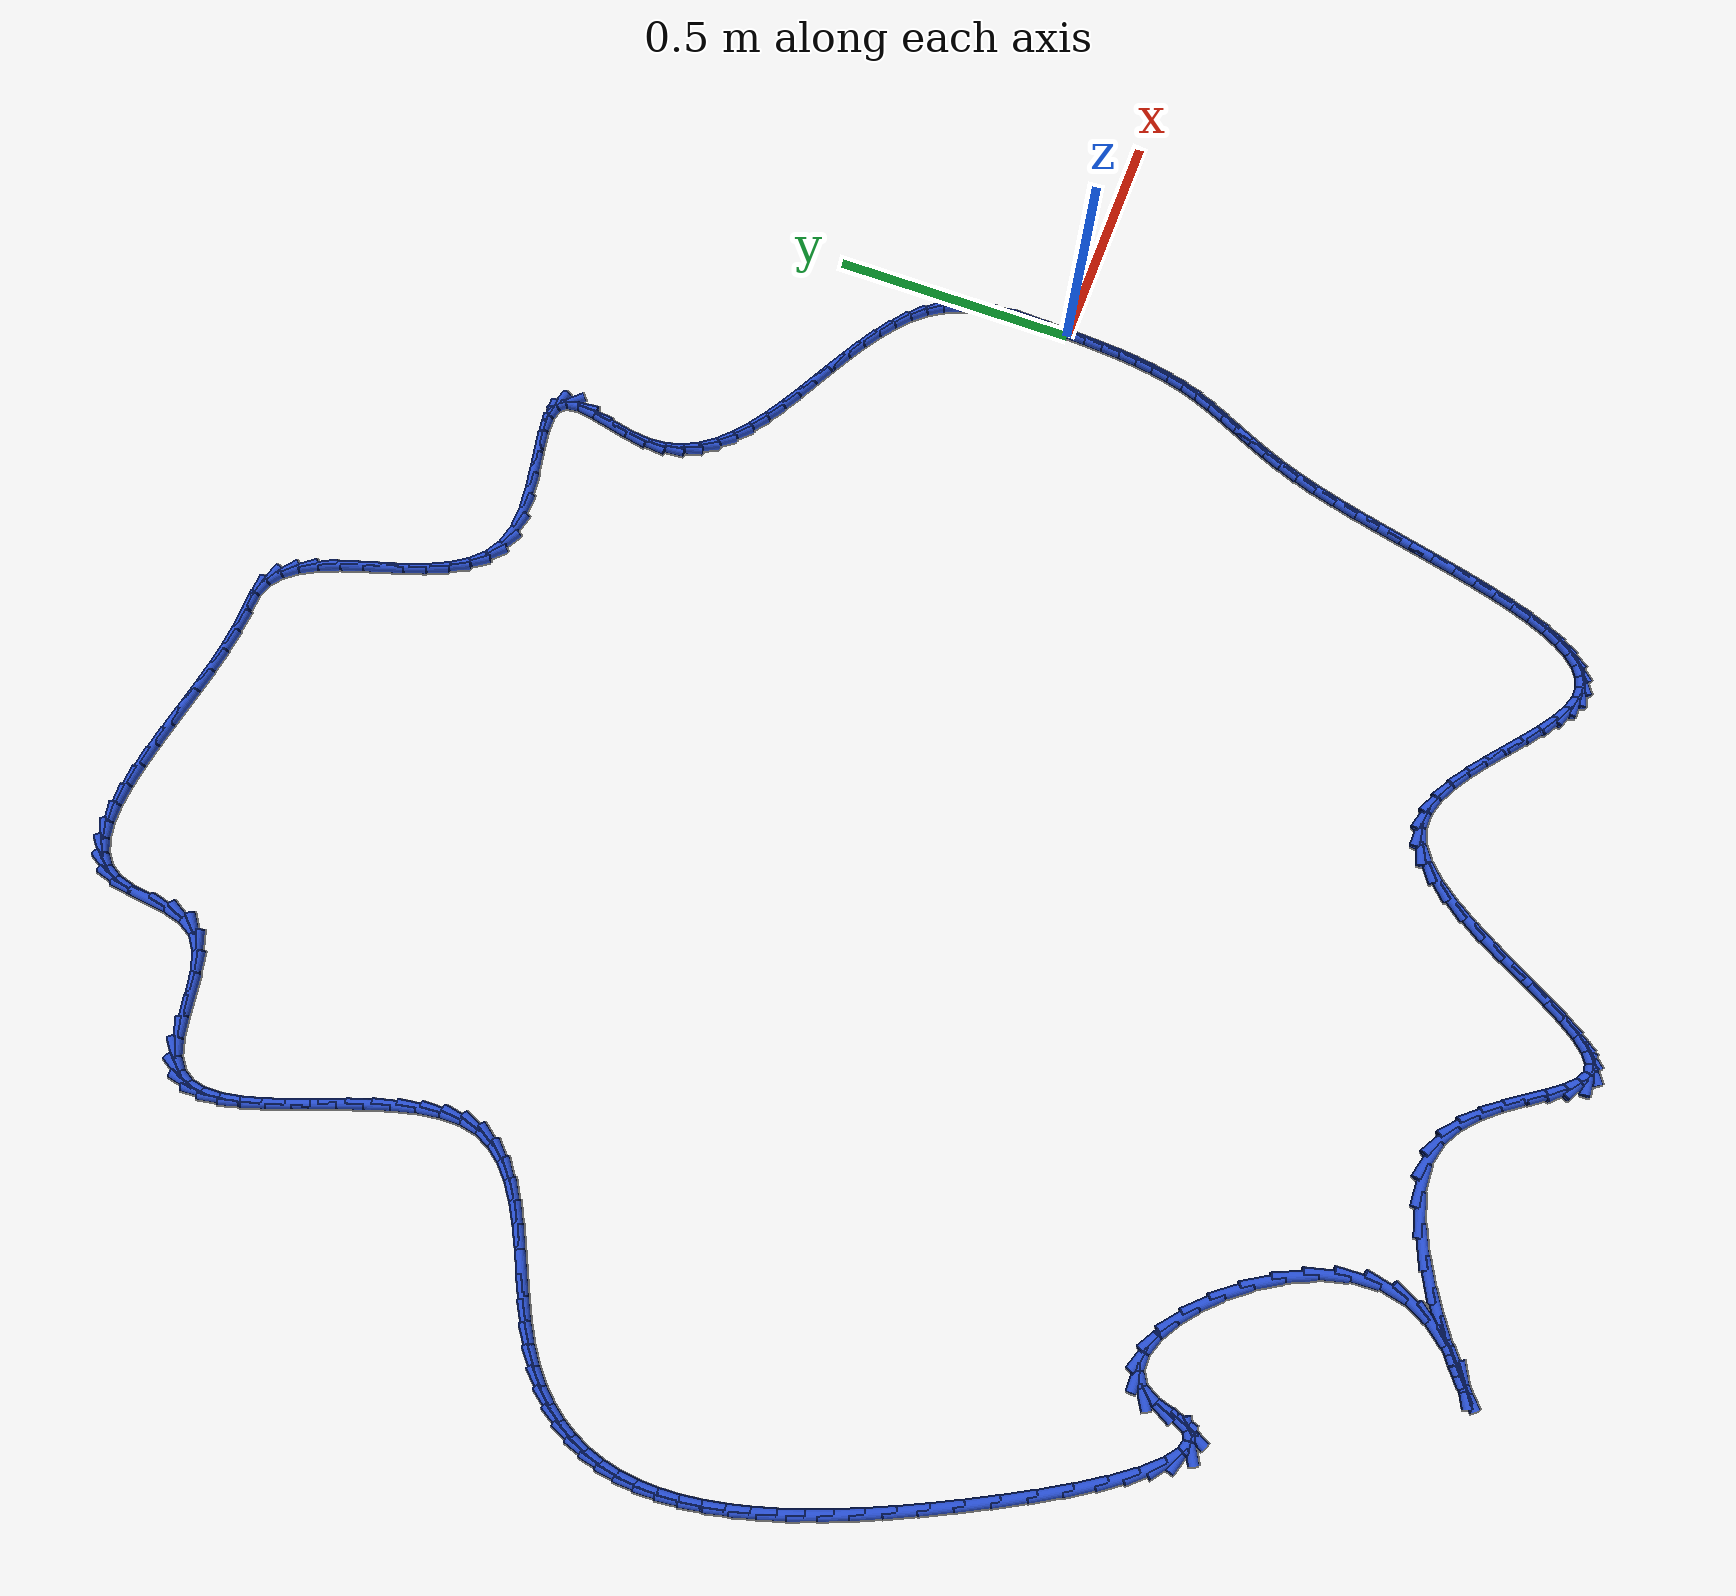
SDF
<sdf version="1.6">
 <world name="default">
  <light name="sun" type="directional">
   <pose>0 0 10 0 -0 0</pose>
   <diffuse>0.8 0.8 0.8 1</diffuse>
   <specular>0.2 0.2 0.2 1</specular>
   <attenuation>
    <range>1000</range>
    <constant>0.9</constant>
    <linear>0.01</linear>
    <quadratic>0.001</quadratic>
   </attenuation>
   <direction>-0.5 0.1 -0.9</direction>
  </light>
  <model name="ground_plane">
   <static>1</static>
   <link name="link">
    <collision name="collision">
     <geometry><plane><normal>0 0 1</normal><size>100 100</size></plane></geometry>
     <surface><friction><ode><mu>100</mu><mu2>50</mu2></ode></friction></surface>
    </collision>
    <visual name="visual">
     <cast_shadows>0</cast_shadows>
     <geometry><plane><normal>0 0 1</normal><size>100 100</size></plane></geometry>
     <material>
      <script><uri>file://media/materials/scripts/gazebo.material</uri><name>Gazebo/WhiteGlow</name></script>
     </material>
    </visual>
   </link>
  </model>
  <gravity>0 0 -9.8</gravity>
  <magnetic_field>6e-06 2.3e-05 -4.2e-05</magnetic_field>
  <atmosphere type="adiabatic"/>
  <physics name="default_physics" default="0" type="ode">
   <max_step_size>0.001</max_step_size>
   <real_time_factor>1</real_time_factor>
   <real_time_update_rate>1000</real_time_update_rate>
  </physics>
  <scene><ambient>0.4 0.4 0.4 1</ambient><background>0.7 0.7 0.7 1</background><shadows>1</shadows></scene>
  <spherical_coordinates>
   <surface_model>EARTH_WGS84</surface_model>
   <latitude_deg>0</latitude_deg>
   <longitude_deg>0</longitude_deg>
   <elevation>0</elevation>
   <heading_deg>0</heading_deg>
  </spherical_coordinates>
  <model name="line">
   <link name="link_0">
    <pose>-2.168404344971009e-19 4.163336342344337e-17 0.01 0 1.57 1.52902783664615</pose>
    <collision name="collision">
     <geometry><cylinder><radius>0.01</radius><length>0.08</length></cylinder></geometry>
    </collision>
    <visual name="visual">
     <material>
      <script><name>Gazebo/Blue</name><uri>file://media/materials/scripts/gazebo.material</uri></script>
     </material>
     <geometry><cylinder><radius>0.01</radius><length>0.08</length></cylinder></geometry>
    </visual>
   </link>
   <link name="link_1">
    <pose>0.001682335990997134 0.04025420916461507 0.01 0 1.57 1.5522324395835811</pose>
    <collision name="collision">
     <geometry><cylinder><radius>0.01</radius><length>0.08</length></cylinder></geometry>
    </collision>
    <visual name="visual">
     <material>
      <script><name>Gazebo/Blue</name><uri>file://media/materials/scripts/gazebo.material</uri></script>
     </material>
     <geometry><cylinder><radius>0.01</radius><length>0.08</length></cylinder></geometry>
    </visual>
   </link>
   <link name="link_2">
    <pose>0.0024287794368318865 0.08045902669245655 0.01 0 1.57 -1.547395278893823</pose>
    <collision name="collision">
     <geometry><cylinder><radius>0.01</radius><length>0.08</length></cylinder></geometry>
    </collision>
    <visual name="visual">
     <material>
      <script><name>Gazebo/Blue</name><uri>file://media/materials/scripts/gazebo.material</uri></script>
     </material>
     <geometry><cylinder><radius>0.01</radius><length>0.08</length></cylinder></geometry>
    </visual>
   </link>
   <link name="link_3">
    <pose>0.0015000876354641073 0.12013768890854712 0.01 0 1.57 -1.4845722345314745</pose>
    <collision name="collision">
     <geometry><cylinder><radius>0.01</radius><length>0.08</length></cylinder></geometry>
    </collision>
    <visual name="visual">
     <material>
      <script><name>Gazebo/Blue</name><uri>file://media/materials/scripts/gazebo.material</uri></script>
     </material>
     <geometry><cylinder><radius>0.01</radius><length>0.08</length></cylinder></geometry>
    </visual>
   </link>
   <link name="link_4">
    <pose>-0.0018429821151463533 0.15881343213790933 0.01 0 1.57 -1.3978798858954011</pose>
    <collision name="collision">
     <geometry><cylinder><radius>0.01</radius><length>0.08</length></cylinder></geometry>
    </collision>
    <visual name="visual">
     <material>
      <script><name>Gazebo/Blue</name><uri>file://media/materials/scripts/gazebo.material</uri></script>
     </material>
     <geometry><cylinder><radius>0.01</radius><length>0.08</length></cylinder></geometry>
    </visual>
   </link>
   <link name="link_5">
    <pose>-0.008339672517039648 0.19600949270556564 0.01 0 1.57 -1.2840930743274215</pose>
    <collision name="collision">
     <geometry><cylinder><radius>0.01</radius><length>0.08</length></cylinder></geometry>
    </collision>
    <visual name="visual">
     <material>
      <script><name>Gazebo/Blue</name><uri>file://media/materials/scripts/gazebo.material</uri></script>
     </material>
     <geometry><cylinder><radius>0.01</radius><length>0.08</length></cylinder></geometry>
    </visual>
   </link>
   <link name="link_6">
    <pose>-0.018729226272255935 0.23124910693653877 0.01 0 1.57 -1.1414021076417333</pose>
    <collision name="collision">
     <geometry><cylinder><radius>0.01</radius><length>0.08</length></cylinder></geometry>
    </collision>
    <visual name="visual">
     <material>
      <script><name>Gazebo/Blue</name><uri>file://media/materials/scripts/gazebo.material</uri></script>
     </material>
     <geometry><cylinder><radius>0.01</radius><length>0.08</length></cylinder></geometry>
    </visual>
   </link>
   <link name="link_7">
    <pose>-0.03375088608283535 0.2640555111558512 0.01 0 1.57 -0.9764500421237643</pose>
    <collision name="collision">
     <geometry><cylinder><radius>0.01</radius><length>0.08</length></cylinder></geometry>
    </collision>
    <visual name="visual">
     <material>
      <script><name>Gazebo/Blue</name><uri>file://media/materials/scripts/gazebo.material</uri></script>
     </material>
     <geometry><cylinder><radius>0.01</radius><length>0.08</length></cylinder></geometry>
    </visual>
   </link>
   <link name="link_8">
    <pose>-0.05401029808813432 0.2940308731569614 0.01 0 1.57 -0.8261137103228651</pose>
    <collision name="collision">
     <geometry><cylinder><radius>0.01</radius><length>0.08</length></cylinder></geometry>
    </collision>
    <visual name="visual">
     <material>
      <script><name>Gazebo/Blue</name><uri>file://media/materials/scripts/gazebo.material</uri></script>
     </material>
     <geometry><cylinder><radius>0.01</radius><length>0.08</length></cylinder></geometry>
    </visual>
   </link>
   <link name="link_9">
    <pose>-0.07917419012969613 0.3213320920714619 0.01 0 1.57 -0.7062568643937363</pose>
    <collision name="collision">
     <geometry><cylinder><radius>0.01</radius><length>0.08</length></cylinder></geometry>
    </collision>
    <visual name="visual">
     <material>
      <script><name>Gazebo/Blue</name><uri>file://media/materials/scripts/gazebo.material</uri></script>
     </material>
     <geometry><cylinder><radius>0.01</radius><length>0.08</length></cylinder></geometry>
    </visual>
   </link>
   <link name="link_10">
    <pose>-0.10850670000065454 0.34635392512444896 0.01 0 1.57 -0.6148824756712293</pose>
    <collision name="collision">
     <geometry><cylinder><radius>0.01</radius><length>0.08</length></cylinder></geometry>
    </collision>
    <visual name="visual">
     <material>
      <script><name>Gazebo/Blue</name><uri>file://media/materials/scripts/gazebo.material</uri></script>
     </material>
     <geometry><cylinder><radius>0.01</radius><length>0.08</length></cylinder></geometry>
    </visual>
   </link>
   <link name="link_11">
    <pose>-0.1412704261000338 0.36949203904523936 0.01 0 1.57 -0.5481707559389956</pose>
    <collision name="collision">
     <geometry><cylinder><radius>0.01</radius><length>0.08</length></cylinder></geometry>
    </collision>
    <visual name="visual">
     <material>
      <script><name>Gazebo/Blue</name><uri>file://media/materials/scripts/gazebo.material</uri></script>
     </material>
     <geometry><cylinder><radius>0.01</radius><length>0.08</length></cylinder></geometry>
    </visual>
   </link>
   <link name="link_12">
    <pose>-0.176727966826858 0.3911421005631499 0.01 0 1.57 -0.5024327338839962</pose>
    <collision name="collision">
     <geometry><cylinder><radius>0.01</radius><length>0.08</length></cylinder></geometry>
    </collision>
    <visual name="visual">
     <material>
      <script><name>Gazebo/Blue</name><uri>file://media/materials/scripts/gazebo.material</uri></script>
     </material>
     <geometry><cylinder><radius>0.01</radius><length>0.08</length></cylinder></geometry>
    </visual>
   </link>
   <link name="link_13">
    <pose>-0.2141419205801512 0.4116997764074969 0.01 0 1.57 -0.47485874763186886</pose>
    <collision name="collision">
     <geometry><cylinder><radius>0.01</radius><length>0.08</length></cylinder></geometry>
    </collision>
    <visual name="visual">
     <material>
      <script><name>Gazebo/Blue</name><uri>file://media/materials/scripts/gazebo.material</uri></script>
     </material>
     <geometry><cylinder><radius>0.01</radius><length>0.08</length></cylinder></geometry>
    </visual>
   </link>
   <link name="link_14">
    <pose>-0.2527748857589378 0.4315607333075975 0.01 0 1.57 -0.46370113612660235</pose>
    <collision name="collision">
     <geometry><cylinder><radius>0.01</radius><length>0.08</length></cylinder></geometry>
    </collision>
    <visual name="visual">
     <material>
      <script><name>Gazebo/Blue</name><uri>file://media/materials/scripts/gazebo.material</uri></script>
     </material>
     <geometry><cylinder><radius>0.01</radius><length>0.08</length></cylinder></geometry>
    </visual>
   </link>
   <link name="link_15">
    <pose>-0.2918894607622417 0.4511206379927679 0.01 0 1.57 -0.4682716443202669</pose>
    <collision name="collision">
     <geometry><cylinder><radius>0.01</radius><length>0.08</length></cylinder></geometry>
    </collision>
    <visual name="visual">
     <material>
      <script><name>Gazebo/Blue</name><uri>file://media/materials/scripts/gazebo.material</uri></script>
     </material>
     <geometry><cylinder><radius>0.01</radius><length>0.08</length></cylinder></geometry>
    </visual>
   </link>
   <link name="link_16">
    <pose>-0.33074824398908714 0.47077515719232504 0.01 0 1.57 -0.4889250011104995</pose>
    <collision name="collision">
     <geometry><cylinder><radius>0.01</radius><length>0.08</length></cylinder></geometry>
    </collision>
    <visual name="visual">
     <material>
      <script><name>Gazebo/Blue</name><uri>file://media/materials/scripts/gazebo.material</uri></script>
     </material>
     <geometry><cylinder><radius>0.01</radius><length>0.08</length></cylinder></geometry>
    </visual>
   </link>
   <link name="link_17">
    <pose>-0.3686138338384983 0.49091995763558555 0.01 0 1.57 -0.527082802370326</pose>
    <collision name="collision">
     <geometry><cylinder><radius>0.01</radius><length>0.08</length></cylinder></geometry>
    </collision>
    <visual name="visual">
     <material>
      <script><name>Gazebo/Blue</name><uri>file://media/materials/scripts/gazebo.material</uri></script>
     </material>
     <geometry><cylinder><radius>0.01</radius><length>0.08</length></cylinder></geometry>
    </visual>
   </link>
   <link name="link_18">
    <pose>-0.4047488287094993 0.5119507060518661 0.01 0 1.57 -0.5852770806005103</pose>
    <collision name="collision">
     <geometry><cylinder><radius>0.01</radius><length>0.08</length></cylinder></geometry>
    </collision>
    <visual name="visual">
     <material>
      <script><name>Gazebo/Blue</name><uri>file://media/materials/scripts/gazebo.material</uri></script>
     </material>
     <geometry><cylinder><radius>0.01</radius><length>0.08</length></cylinder></geometry>
    </visual>
   </link>
   <link name="link_19">
    <pose>-0.43841582700111426 0.5342630691704833 0.01 0 1.57 -0.6670953673856461</pose>
    <collision name="collision">
     <geometry><cylinder><radius>0.01</radius><length>0.08</length></cylinder></geometry>
    </collision>
    <visual name="visual">
     <material>
      <script><name>Gazebo/Blue</name><uri>file://media/materials/scripts/gazebo.material</uri></script>
     </material>
     <geometry><cylinder><radius>0.01</radius><length>0.08</length></cylinder></geometry>
    </visual>
   </link>
   <link name="link_20">
    <pose>-0.4688774271123673 0.5582527137207538 0.01 0 1.57 -0.7767221632854268</pose>
    <collision name="collision">
     <geometry><cylinder><radius>0.01</radius><length>0.08</length></cylinder></geometry>
    </collision>
    <visual name="visual">
     <material>
      <script><name>Gazebo/Blue</name><uri>file://media/materials/scripts/gazebo.material</uri></script>
     </material>
     <geometry><cylinder><radius>0.01</radius><length>0.08</length></cylinder></geometry>
    </visual>
   </link>
   <link name="link_21">
    <pose>-0.4953962274422826 0.5843153064319944 0.01 0 1.57 -0.9174938906017656</pose>
    <collision name="collision">
     <geometry><cylinder><radius>0.01</radius><length>0.08</length></cylinder></geometry>
    </collision>
    <visual name="visual">
     <material>
      <script><name>Gazebo/Blue</name><uri>file://media/materials/scripts/gazebo.material</uri></script>
     </material>
     <geometry><cylinder><radius>0.01</radius><length>0.08</length></cylinder></geometry>
    </visual>
   </link>
   <link name="link_22">
    <pose>-0.5172348263898843 0.6128465140335215 0.01 0 1.57 -1.088889585105464</pose>
    <collision name="collision">
     <geometry><cylinder><radius>0.01</radius><length>0.08</length></cylinder></geometry>
    </collision>
    <visual name="visual">
     <material>
      <script><name>Gazebo/Blue</name><uri>file://media/materials/scripts/gazebo.material</uri></script>
     </material>
     <geometry><cylinder><radius>0.01</radius><length>0.08</length></cylinder></geometry>
    </visual>
   </link>
   <link name="link_23">
    <pose>-0.5336558223541966 0.644242003254652 0.01 0 1.57 -1.2828015319334976</pose>
    <collision name="collision">
     <geometry><cylinder><radius>0.01</radius><length>0.08</length></cylinder></geometry>
    </collision>
    <visual name="visual">
     <material>
      <script><name>Gazebo/Blue</name><uri>file://media/materials/scripts/gazebo.material</uri></script>
     </material>
     <geometry><cylinder><radius>0.01</radius><length>0.08</length></cylinder></geometry>
    </visual>
   </link>
   <link name="link_24">
    <pose>-0.5439218137342436 0.6788974408247026 0.01 0 1.57 -1.4829651259856962</pose>
    <collision name="collision">
     <geometry><cylinder><radius>0.01</radius><length>0.08</length></cylinder></geometry>
    </collision>
    <visual name="visual">
     <material>
      <script><name>Gazebo/Blue</name><uri>file://media/materials/scripts/gazebo.material</uri></script>
     </material>
     <geometry><cylinder><radius>0.01</radius><length>0.08</length></cylinder></geometry>
    </visual>
   </link>
   <link name="link_25">
    <pose>-0.5472953989290498 0.7172084934729901 0.01 0 1.57 1.4776111202885178</pose>
    <collision name="collision">
     <geometry><cylinder><radius>0.01</radius><length>0.08</length></cylinder></geometry>
    </collision>
    <visual name="visual">
     <material>
      <script><name>Gazebo/Blue</name><uri>file://media/materials/scripts/gazebo.material</uri></script>
     </material>
     <geometry><cylinder><radius>0.01</radius><length>0.08</length></cylinder></geometry>
    </visual>
   </link>
   <link name="link_26">
    <pose>-0.5433597274383125 0.759321112624327 0.01 0 1.57 1.3759694845394403</pose>
    <collision name="collision">
     <geometry><cylinder><radius>0.01</radius><length>0.08</length></cylinder></geometry>
    </collision>
    <visual name="visual">
     <material>
      <script><name>Gazebo/Blue</name><uri>file://media/materials/scripts/gazebo.material</uri></script>
     </material>
     <geometry><cylinder><radius>0.01</radius><length>0.08</length></cylinder></geometry>
    </visual>
   </link>
   <link name="link_27">
    <pose>-0.5347380154660346 0.8030129808653238 0.01 0 1.57 1.3582862790561092</pose>
    <collision name="collision">
     <geometry><cylinder><radius>0.01</radius><length>0.08</length></cylinder></geometry>
    </collision>
    <visual name="visual">
     <material>
      <script><name>Gazebo/Blue</name><uri>file://media/materials/scripts/gazebo.material</uri></script>
     </material>
     <geometry><cylinder><radius>0.01</radius><length>0.08</length></cylinder></geometry>
    </visual>
   </link>
   <link name="link_28">
    <pose>-0.5257315225989049 0.8447545535935493 0.01 0 1.57 1.4317631129664112</pose>
    <collision name="collision">
     <geometry><cylinder><radius>0.01</radius><length>0.08</length></cylinder></geometry>
    </collision>
    <visual name="visual">
     <material>
      <script><name>Gazebo/Blue</name><uri>file://media/materials/scripts/gazebo.material</uri></script>
     </material>
     <geometry><cylinder><radius>0.01</radius><length>0.08</length></cylinder></geometry>
    </visual>
   </link>
   <link name="link_29">
    <pose>-0.5206591189850854 0.8810025672497138 0.01 0 1.57 -1.4544401839341699</pose>
    <collision name="collision">
     <geometry><cylinder><radius>0.01</radius><length>0.08</length></cylinder></geometry>
    </collision>
    <visual name="visual">
     <material>
      <script><name>Gazebo/Blue</name><uri>file://media/materials/scripts/gazebo.material</uri></script>
     </material>
     <geometry><cylinder><radius>0.01</radius><length>0.08</length></cylinder></geometry>
    </visual>
   </link>
   <link name="link_30">
    <pose>-0.5238396747727394 0.9082137582745284 0.01 0 1.57 -0.7975469096733435</pose>
    <collision name="collision">
     <geometry><cylinder><radius>0.01</radius><length>0.08</length></cylinder></geometry>
    </collision>
    <visual name="visual">
     <material>
      <script><name>Gazebo/Blue</name><uri>file://media/materials/scripts/gazebo.material</uri></script>
     </material>
     <geometry><cylinder><radius>0.01</radius><length>0.08</length></cylinder></geometry>
    </visual>
   </link>
   <link name="link_31">
    <pose>-0.5388274271244949 0.9235701723424261 0.01 0 1.57 -0.1825803853555193</pose>
    <collision name="collision">
     <geometry><cylinder><radius>0.01</radius><length>0.08</length></cylinder></geometry>
    </collision>
    <visual name="visual">
     <material>
      <script><name>Gazebo/Blue</name><uri>file://media/materials/scripts/gazebo.material</uri></script>
     </material>
     <geometry><cylinder><radius>0.01</radius><length>0.08</length></cylinder></geometry>
    </visual>
   </link>
   <link name="link_32">
    <pose>-0.5648350565355627 0.9283721330457155 0.01 0 1.57 0.08623113423185368</pose>
    <collision name="collision">
     <geometry><cylinder><radius>0.01</radius><length>0.08</length></cylinder></geometry>
    </collision>
    <visual name="visual">
     <material>
      <script><name>Gazebo/Blue</name><uri>file://media/materials/scripts/gazebo.material</uri></script>
     </material>
     <geometry><cylinder><radius>0.01</radius><length>0.08</length></cylinder></geometry>
    </visual>
   </link>
   <link name="link_33">
    <pose>-0.5995448784784578 0.9253716249734535 0.01 0 1.57 0.19343416865101154</pose>
    <collision name="collision">
     <geometry><cylinder><radius>0.01</radius><length>0.08</length></cylinder></geometry>
    </collision>
    <visual name="visual">
     <material>
      <script><name>Gazebo/Blue</name><uri>file://media/materials/scripts/gazebo.material</uri></script>
     </material>
     <geometry><cylinder><radius>0.01</radius><length>0.08</length></cylinder></geometry>
    </visual>
   </link>
   <link name="link_34">
    <pose>-0.640637487300593 0.9173222653253129 0.01 0 1.57 0.22519990240933957</pose>
    <collision name="collision">
     <geometry><cylinder><radius>0.01</radius><length>0.08</length></cylinder></geometry>
    </collision>
    <visual name="visual">
     <material>
      <script><name>Gazebo/Blue</name><uri>file://media/materials/scripts/gazebo.material</uri></script>
     </material>
     <geometry><cylinder><radius>0.01</radius><length>0.08</length></cylinder></geometry>
    </visual>
   </link>
   <link name="link_35">
    <pose>-0.6857934773493802 0.906977671300966 0.01 0 1.57 0.2077521247927817</pose>
    <collision name="collision">
     <geometry><cylinder><radius>0.01</radius><length>0.08</length></cylinder></geometry>
    </collision>
    <visual name="visual">
     <material>
      <script><name>Gazebo/Blue</name><uri>file://media/materials/scripts/gazebo.material</uri></script>
     </material>
     <geometry><cylinder><radius>0.01</radius><length>0.08</length></cylinder></geometry>
    </visual>
   </link>
   <link name="link_36">
    <pose>-0.7326934429722315 0.8970914601000852 0.01 0 1.57 0.14309042923364193</pose>
    <collision name="collision">
     <geometry><cylinder><radius>0.01</radius><length>0.08</length></cylinder></geometry>
    </collision>
    <visual name="visual">
     <material>
      <script><name>Gazebo/Blue</name><uri>file://media/materials/scripts/gazebo.material</uri></script>
     </material>
     <geometry><cylinder><radius>0.01</radius><length>0.08</length></cylinder></geometry>
    </visual>
   </link>
   <link name="link_37">
    <pose>-0.7790179785165596 0.8904172489223436 0.01 0 1.57 0.016314436669079748</pose>
    <collision name="collision">
     <geometry><cylinder><radius>0.01</radius><length>0.08</length></cylinder></geometry>
    </collision>
    <visual name="visual">
     <material>
      <script><name>Gazebo/Blue</name><uri>file://media/materials/scripts/gazebo.material</uri></script>
     </material>
     <geometry><cylinder><radius>0.01</radius><length>0.08</length></cylinder></geometry>
    </visual>
   </link>
   <link name="link_38">
    <pose>-0.8224476783297759 0.8897086549674132 0.01 0 1.57 -0.20586333262047113</pose>
    <collision name="collision">
     <geometry><cylinder><radius>0.01</radius><length>0.08</length></cylinder></geometry>
    </collision>
    <visual name="visual">
     <material>
      <script><name>Gazebo/Blue</name><uri>file://media/materials/scripts/gazebo.material</uri></script>
     </material>
     <geometry><cylinder><radius>0.01</radius><length>0.08</length></cylinder></geometry>
    </visual>
   </link>
   <link name="link_39">
    <pose>-0.8606828662853225 0.8976929894097176 0.01 0 1.57 -0.5078108951536892</pose>
    <collision name="collision">
     <geometry><cylinder><radius>0.01</radius><length>0.08</length></cylinder></geometry>
    </collision>
    <visual name="visual">
     <material>
      <script><name>Gazebo/Blue</name><uri>file://media/materials/scripts/gazebo.material</uri></script>
     </material>
     <geometry><cylinder><radius>0.01</radius><length>0.08</length></cylinder></geometry>
    </visual>
   </link>
   <link name="link_40">
    <pose>-0.8926396271941479 0.9154765494230397 0.01 0 1.57 -0.7788302168026623</pose>
    <collision name="collision">
     <geometry><cylinder><radius>0.01</radius><length>0.08</length></cylinder></geometry>
    </collision>
    <visual name="visual">
     <material>
      <script><name>Gazebo/Blue</name><uri>file://media/materials/scripts/gazebo.material</uri></script>
     </material>
     <geometry><cylinder><radius>0.01</radius><length>0.08</length></cylinder></geometry>
    </visual>
   </link>
   <link name="link_41">
    <pose>-0.9191371030563574 0.9416282235077327 0.01 0 1.57 -0.9804470711389746</pose>
    <collision name="collision">
     <geometry><cylinder><radius>0.01</radius><length>0.08</length></cylinder></geometry>
    </collision>
    <visual name="visual">
     <material>
      <script><name>Gazebo/Blue</name><uri>file://media/materials/scripts/gazebo.material</uri></script>
     </material>
     <geometry><cylinder><radius>0.01</radius><length>0.08</length></cylinder></geometry>
    </visual>
   </link>
   <link name="link_42">
    <pose>-0.9411603363959884 0.9744956995450904 0.01 0 1.57 -1.1162897351473104</pose>
    <collision name="collision">
     <geometry><cylinder><radius>0.01</radius><length>0.08</length></cylinder></geometry>
    </collision>
    <visual name="visual">
     <material>
      <script><name>Gazebo/Blue</name><uri>file://media/materials/scripts/gazebo.material</uri></script>
     </material>
     <geometry><cylinder><radius>0.01</radius><length>0.08</length></cylinder></geometry>
    </visual>
   </link>
   <link name="link_43">
    <pose>-0.9596943697370772 1.0124266654164067 0.01 0 1.57 -1.2009060556589932</pose>
    <collision name="collision">
     <geometry><cylinder><radius>0.01</radius><length>0.08</length></cylinder></geometry>
    </collision>
    <visual name="visual">
     <material>
      <script><name>Gazebo/Blue</name><uri>file://media/materials/scripts/gazebo.material</uri></script>
     </material>
     <geometry><cylinder><radius>0.01</radius><length>0.08</length></cylinder></geometry>
    </visual>
   </link>
   <link name="link_44">
    <pose>-0.975724245603661 1.0537688090029755 0.01 0 1.57 -1.2460469481754417</pose>
    <collision name="collision">
     <geometry><cylinder><radius>0.01</radius><length>0.08</length></cylinder></geometry>
    </collision>
    <visual name="visual">
     <material>
      <script><name>Gazebo/Blue</name><uri>file://media/materials/scripts/gazebo.material</uri></script>
     </material>
     <geometry><cylinder><radius>0.01</radius><length>0.08</length></cylinder></geometry>
    </visual>
   </link>
   <link name="link_45">
    <pose>-0.9902350065197768 1.0968698181860908 0.01 0 1.57 -1.2579417963438402</pose>
    <collision name="collision">
     <geometry><cylinder><radius>0.01</radius><length>0.08</length></cylinder></geometry>
    </collision>
    <visual name="visual">
     <material>
      <script><name>Gazebo/Blue</name><uri>file://media/materials/scripts/gazebo.material</uri></script>
     </material>
     <geometry><cylinder><radius>0.01</radius><length>0.08</length></cylinder></geometry>
    </visual>
   </link>
   <link name="link_46">
    <pose>-1.0042116950094613 1.1400773808470461 0.01 0 1.57 -1.2374177473726158</pose>
    <collision name="collision">
     <geometry><cylinder><radius>0.01</radius><length>0.08</length></cylinder></geometry>
    </collision>
    <visual name="visual">
     <material>
      <script><name>Gazebo/Blue</name><uri>file://media/materials/scripts/gazebo.material</uri></script>
     </material>
     <geometry><cylinder><radius>0.01</radius><length>0.08</length></cylinder></geometry>
    </visual>
   </link>
   <link name="link_47">
    <pose>-1.0186393535967517 1.1817391848671355 0.01 0 1.57 -1.1796189326627855</pose>
    <collision name="collision">
     <geometry><cylinder><radius>0.01</radius><length>0.08</length></cylinder></geometry>
    </collision>
    <visual name="visual">
     <material>
      <script><name>Gazebo/Blue</name><uri>file://media/materials/scripts/gazebo.material</uri></script>
     </material>
     <geometry><cylinder><radius>0.01</radius><length>0.08</length></cylinder></geometry>
    </visual>
   </link>
   <link name="link_48">
    <pose>-1.0345030248056843 1.2202029181276524 0.01 0 1.57 -1.0725928029355911</pose>
    <collision name="collision">
     <geometry><cylinder><radius>0.01</radius><length>0.08</length></cylinder></geometry>
    </collision>
    <visual name="visual">
     <material>
      <script><name>Gazebo/Blue</name><uri>file://media/materials/scripts/gazebo.material</uri></script>
     </material>
     <geometry><cylinder><radius>0.01</radius><length>0.08</length></cylinder></geometry>
    </visual>
   </link>
   <link name="link_49">
    <pose>-1.0527877511602963 1.2538162685098906 0.01 0 1.57 -0.896003662918484</pose>
    <collision name="collision">
     <geometry><cylinder><radius>0.01</radius><length>0.08</length></cylinder></geometry>
    </collision>
    <visual name="visual">
     <material>
      <script><name>Gazebo/Blue</name><uri>file://media/materials/scripts/gazebo.material</uri></script>
     </material>
     <geometry><cylinder><radius>0.01</radius><length>0.08</length></cylinder></geometry>
    </visual>
   </link>
   <link name="link_50">
    <pose>-1.0744785751846244 1.2809269238951444 0.01 0 1.57 -0.6284688805906374</pose>
    <collision name="collision">
     <geometry><cylinder><radius>0.01</radius><length>0.08</length></cylinder></geometry>
    </collision>
    <visual name="visual">
     <material>
      <script><name>Gazebo/Blue</name><uri>file://media/materials/scripts/gazebo.material</uri></script>
     </material>
     <geometry><cylinder><radius>0.01</radius><length>0.08</length></cylinder></geometry>
    </visual>
   </link>
   <link name="link_51">
    <pose>-1.1005605394027058 1.2998825721647074 0.01 0 1.57 -0.2833354514659433</pose>
    <collision name="collision">
     <geometry><cylinder><radius>0.01</radius><length>0.08</length></cylinder></geometry>
    </collision>
    <visual name="visual">
     <material>
      <script><name>Gazebo/Blue</name><uri>file://media/materials/scripts/gazebo.material</uri></script>
     </material>
     <geometry><cylinder><radius>0.01</radius><length>0.08</length></cylinder></geometry>
    </visual>
   </link>
   <link name="link_52">
    <pose>-1.1320157269772946 1.3090413494905073 0.01 0 1.57 -0.011447405670382469</pose>
    <collision name="collision">
     <geometry><cylinder><radius>0.01</radius><length>0.08</length></cylinder></geometry>
    </collision>
    <visual name="visual">
     <material>
      <script><name>Gazebo/Blue</name><uri>file://media/materials/scripts/gazebo.material</uri></script>
     </material>
     <geometry><cylinder><radius>0.01</radius><length>0.08</length></cylinder></geometry>
    </visual>
   </link>
   <link name="link_53">
    <pose>-1.1690603318638493 1.309465432635094 0.01 0 1.57 0.025244809828127657</pose>
    <collision name="collision">
     <geometry><cylinder><radius>0.01</radius><length>0.08</length></cylinder></geometry>
    </collision>
    <visual name="visual">
     <material>
      <script><name>Gazebo/Blue</name><uri>file://media/materials/scripts/gazebo.material</uri></script>
     </material>
     <geometry><cylinder><radius>0.01</radius><length>0.08</length></cylinder></geometry>
    </visual>
   </link>
   <link name="link_54">
    <pose>-1.2101382748947689 1.3084282074244304 0.01 0 1.57 -0.04664727080863376</pose>
    <collision name="collision">
     <geometry><cylinder><radius>0.01</radius><length>0.08</length></cylinder></geometry>
    </collision>
    <visual name="visual">
     <material>
      <script><name>Gazebo/Blue</name><uri>file://media/materials/scripts/gazebo.material</uri></script>
     </material>
     <geometry><cylinder><radius>0.01</radius><length>0.08</length></cylinder></geometry>
    </visual>
   </link>
   <link name="link_55">
    <pose>-1.253890275954914 1.310470600475133 0.01 0 1.57 -0.1020195654637777</pose>
    <collision name="collision">
     <geometry><cylinder><radius>0.01</radius><length>0.08</length></cylinder></geometry>
    </collision>
    <visual name="visual">
     <material>
      <script><name>Gazebo/Blue</name><uri>file://media/materials/scripts/gazebo.material</uri></script>
     </material>
     <geometry><cylinder><radius>0.01</radius><length>0.08</length></cylinder></geometry>
    </visual>
   </link>
   <link name="link_56">
    <pose>-1.299575607714188 1.3151476356203005 0.01 0 1.57 -0.13773700441533812</pose>
    <collision name="collision">
     <geometry><cylinder><radius>0.01</radius><length>0.08</length></cylinder></geometry>
    </collision>
    <visual name="visual">
     <material>
      <script><name>Gazebo/Blue</name><uri>file://media/materials/scripts/gazebo.material</uri></script>
     </material>
     <geometry><cylinder><radius>0.01</radius><length>0.08</length></cylinder></geometry>
    </visual>
   </link>
   <link name="link_57">
    <pose>-1.346498514329996 1.3216518397968404 0.01 0 1.57 -0.15720759408814997</pose>
    <collision name="collision">
     <geometry><cylinder><radius>0.01</radius><length>0.08</length></cylinder></geometry>
    </collision>
    <visual name="visual">
     <material>
      <script><name>Gazebo/Blue</name><uri>file://media/materials/scripts/gazebo.material</uri></script>
     </material>
     <geometry><cylinder><radius>0.01</radius><length>0.08</length></cylinder></geometry>
    </visual>
   </link>
   <link name="link_58">
    <pose>-1.3939632399597408 1.3291757399416597 0.01 0 1.57 -0.1620826792132219</pose>
    <collision name="collision">
     <geometry><cylinder><radius>0.01</radius><length>0.08</length></cylinder></geometry>
    </collision>
    <visual name="visual">
     <material>
      <script><name>Gazebo/Blue</name><uri>file://media/materials/scripts/gazebo.material</uri></script>
     </material>
     <geometry><cylinder><radius>0.01</radius><length>0.08</length></cylinder></geometry>
    </visual>
   </link>
   <link name="link_59">
    <pose>-1.4412740287608288 1.3369118629916665 0.01 0 1.57 -0.1525023961799148</pose>
    <collision name="collision">
     <geometry><cylinder><radius>0.01</radius><length>0.08</length></cylinder></geometry>
    </collision>
    <visual name="visual">
     <material>
      <script><name>Gazebo/Blue</name><uri>file://media/materials/scripts/gazebo.material</uri></script>
     </material>
     <geometry><cylinder><radius>0.01</radius><length>0.08</length></cylinder></geometry>
    </visual>
   </link>
   <link name="link_60">
    <pose>-1.4877351248906625 1.3440527358837666 0.01 0 1.57 -0.12706561280483658</pose>
    <collision name="collision">
     <geometry><cylinder><radius>0.01</radius><length>0.08</length></cylinder></geometry>
    </collision>
    <visual name="visual">
     <material>
      <script><name>Gazebo/Blue</name><uri>file://media/materials/scripts/gazebo.material</uri></script>
     </material>
     <geometry><cylinder><radius>0.01</radius><length>0.08</length></cylinder></geometry>
    </visual>
   </link>
   <link name="link_61">
    <pose>-1.5326507725066474 1.3497908855548688 0.01 0 1.57 -0.08248376761253384</pose>
    <collision name="collision">
     <geometry><cylinder><radius>0.01</radius><length>0.08</length></cylinder></geometry>
    </collision>
    <visual name="visual">
     <material>
      <script><name>Gazebo/Blue</name><uri>file://media/materials/scripts/gazebo.material</uri></script>
     </material>
     <geometry><cylinder><radius>0.01</radius><length>0.08</length></cylinder></geometry>
    </visual>
   </link>
   <link name="link_62">
    <pose>-1.5753252157661868 1.3533188389418793 0.01 0 1.57 -0.012840672194655829</pose>
    <collision name="collision">
     <geometry><cylinder><radius>0.01</radius><length>0.08</length></cylinder></geometry>
    </collision>
    <visual name="visual">
     <material>
      <script><name>Gazebo/Blue</name><uri>file://media/materials/scripts/gazebo.material</uri></script>
     </material>
     <geometry><cylinder><radius>0.01</radius><length>0.08</length></cylinder></geometry>
    </visual>
   </link>
   <link name="link_63">
    <pose>-1.615062698826686 1.3538291229817059 0.01 0 1.57 0.09155552827843134</pose>
    <collision name="collision">
     <geometry><cylinder><radius>0.01</radius><length>0.08</length></cylinder></geometry>
    </collision>
    <visual name="visual">
     <material>
      <script><name>Gazebo/Blue</name><uri>file://media/materials/scripts/gazebo.material</uri></script>
     </material>
     <geometry><cylinder><radius>0.01</radius><length>0.08</length></cylinder></geometry>
    </visual>
   </link>
   <link name="link_64">
    <pose>-1.6511674658455484 1.3505142646112551 0.01 0 1.57 0.24507936637229677</pose>
    <collision name="collision">
     <geometry><cylinder><radius>0.01</radius><length>0.08</length></cylinder></geometry>
    </collision>
    <visual name="visual">
     <material>
      <script><name>Gazebo/Blue</name><uri>file://media/materials/scripts/gazebo.material</uri></script>
     </material>
     <geometry><cylinder><radius>0.01</radius><length>0.08</length></cylinder></geometry>
    </visual>
   </link>
   <link name="link_65">
    <pose>-1.6829437609801796 1.3425667907674357 0.01 0 1.57 0.46399230576907846</pose>
    <collision name="collision">
     <geometry><cylinder><radius>0.01</radius><length>0.08</length></cylinder></geometry>
    </collision>
    <visual name="visual">
     <material>
      <script><name>Gazebo/Blue</name><uri>file://media/materials/scripts/gazebo.material</uri></script>
     </material>
     <geometry><cylinder><radius>0.01</radius><length>0.08</length></cylinder></geometry>
    </visual>
   </link>
   <link name="link_66">
    <pose>-1.709695828387983 1.3291792283871535 0.01 0 1.57 0.7510606503273874</pose>
    <collision name="collision">
     <geometry><cylinder><radius>0.01</radius><length>0.08</length></cylinder></geometry>
    </collision>
    <visual name="visual">
     <material>
      <script><name>Gazebo/Blue</name><uri>file://media/materials/scripts/gazebo.material</uri></script>
     </material>
     <geometry><cylinder><radius>0.01</radius><length>0.08</length></cylinder></geometry>
    </visual>
   </link>
   <link name="link_67">
    <pose>-1.7307279122263628 1.3095441044073166 0.01 0 1.57 1.0697741440407686</pose>
    <collision name="collision">
     <geometry><cylinder><radius>0.01</radius><length>0.08</length></cylinder></geometry>
    </collision>
    <visual name="visual">
     <material>
      <script><name>Gazebo/Blue</name><uri>file://media/materials/scripts/gazebo.material</uri></script>
     </material>
     <geometry><cylinder><radius>0.01</radius><length>0.08</length></cylinder></geometry>
    </visual>
   </link>
   <link name="link_68">
    <pose>-1.7453442566527242 1.2828539457648316 0.01 0 1.57 1.345590347891937</pose>
    <collision name="collision">
     <geometry><cylinder><radius>0.01</radius><length>0.08</length></cylinder></geometry>
    </collision>
    <visual name="visual">
     <material>
      <script><name>Gazebo/Blue</name><uri>file://media/materials/scripts/gazebo.material</uri></script>
     </material>
     <geometry><cylinder><radius>0.01</radius><length>0.08</length></cylinder></geometry>
    </visual>
   </link>
   <link name="link_69">
    <pose>-1.7531857191021087 1.248625525137174 0.01 0 1.57 1.4769746714853549</pose>
    <collision name="collision">
     <geometry><cylinder><radius>0.01</radius><length>0.08</length></cylinder></geometry>
    </collision>
    <visual name="visual">
     <material>
      <script><name>Gazebo/Blue</name><uri>file://media/materials/scripts/gazebo.material</uri></script>
     </material>
     <geometry><cylinder><radius>0.01</radius><length>0.08</length></cylinder></geometry>
    </visual>
   </link>
   <link name="link_70">
    <pose>-1.7568897357363 1.2092620963746297 0.01 0 1.57 1.4780227258974552</pose>
    <collision name="collision">
     <geometry><cylinder><radius>0.01</radius><length>0.08</length></cylinder></geometry>
    </collision>
    <visual name="visual">
     <material>
      <script><name>Gazebo/Blue</name><uri>file://media/materials/scripts/gazebo.material</uri></script>
     </material>
     <geometry><cylinder><radius>0.01</radius><length>0.08</length></cylinder></geometry>
    </visual>
   </link>
   <link name="link_71">
    <pose>-1.760665441256584 1.1686808659572385 0.01 0 1.57 1.3608209402405416</pose>
    <collision name="collision">
     <geometry><cylinder><radius>0.01</radius><length>0.08</length></cylinder></geometry>
    </collision>
    <visual name="visual">
     <material>
      <script><name>Gazebo/Blue</name><uri>file://media/materials/scripts/gazebo.material</uri></script>
     </material>
     <geometry><cylinder><radius>0.01</radius><length>0.08</length></cylinder></geometry>
    </visual>
   </link>
   <link name="link_72">
    <pose>-1.7687358434473825 1.130812403736046 0.01 0 1.57 1.0825146848429377</pose>
    <collision name="collision">
     <geometry><cylinder><radius>0.01</radius><length>0.08</length></cylinder></geometry>
    </collision>
    <visual name="visual">
     <material>
      <script><name>Gazebo/Blue</name><uri>file://media/materials/scripts/gazebo.material</uri></script>
     </material>
     <geometry><cylinder><radius>0.01</radius><length>0.08</length></cylinder></geometry>
    </visual>
   </link>
   <link name="link_73">
    <pose>-1.7853226657203982 1.0995862077415397 0.01 0 1.57 0.6760642856665121</pose>
    <collision name="collision">
     <geometry><cylinder><radius>0.01</radius><length>0.08</length></cylinder></geometry>
    </collision>
    <visual name="visual">
     <material>
      <script><name>Gazebo/Blue</name><uri>file://media/materials/scripts/gazebo.material</uri></script>
     </material>
     <geometry><cylinder><radius>0.01</radius><length>0.08</length></cylinder></geometry>
    </visual>
   </link>
   <link name="link_74">
    <pose>-1.8128945404063046 1.0774688057631645 0.01 0 1.57 0.3944374071200519</pose>
    <collision name="collision">
     <geometry><cylinder><radius>0.01</radius><length>0.08</length></cylinder></geometry>
    </collision>
    <visual name="visual">
     <material>
      <script><name>Gazebo/Blue</name><uri>file://media/materials/scripts/gazebo.material</uri></script>
     </material>
     <geometry><cylinder><radius>0.01</radius><length>0.08</length></cylinder></geometry>
    </visual>
   </link>
   <link name="link_75">
    <pose>-1.8486953790097813 1.0625666491694188 0.01 0 1.57 0.25227227049008477</pose>
    <collision name="collision">
     <geometry><cylinder><radius>0.01</radius><length>0.08</length></cylinder></geometry>
    </collision>
    <visual name="visual">
     <material>
      <script><name>Gazebo/Blue</name><uri>file://media/materials/scripts/gazebo.material</uri></script>
     </material>
     <geometry><cylinder><radius>0.01</radius><length>0.08</length></cylinder></geometry>
    </visual>
   </link>
   <link name="link_76">
    <pose>-1.8890000973654983 1.0521775537454803 0.01 0 1.57 0.20584215326226246</pose>
    <collision name="collision">
     <geometry><cylinder><radius>0.01</radius><length>0.08</length></cylinder></geometry>
    </collision>
    <visual name="visual">
     <material>
      <script><name>Gazebo/Blue</name><uri>file://media/materials/scripts/gazebo.material</uri></script>
     </material>
     <geometry><cylinder><radius>0.01</radius><length>0.08</length></cylinder></geometry>
    </visual>
   </link>
   <link name="link_77">
    <pose>-1.9300836113081277 1.043599335276528 0.01 0 1.57 0.2433793251217469</pose>
    <collision name="collision">
     <geometry><cylinder><radius>0.01</radius><length>0.08</length></cylinder></geometry>
    </collision>
    <visual name="visual">
     <material>
      <script><name>Gazebo/Blue</name><uri>file://media/materials/scripts/gazebo.material</uri></script>
     </material>
     <geometry><cylinder><radius>0.01</radius><length>0.08</length></cylinder></geometry>
    </visual>
   </link>
   <link name="link_78">
    <pose>-1.9682208366723393 1.0341298095477407 0.01 0 1.57 0.39349726225751896</pose>
    <collision name="collision">
     <geometry><cylinder><radius>0.01</radius><length>0.08</length></cylinder></geometry>
    </collision>
    <visual name="visual">
     <material>
      <script><name>Gazebo/Blue</name><uri>file://media/materials/scripts/gazebo.material</uri></script>
     </material>
     <geometry><cylinder><radius>0.01</radius><length>0.08</length></cylinder></geometry>
    </visual>
   </link>
   <link name="link_79">
    <pose>-1.9996866892928034 1.0210667923442962 0.01 0 1.57 0.7098550646958778</pose>
    <collision name="collision">
     <geometry><cylinder><radius>0.01</radius><length>0.08</length></cylinder></geometry>
    </collision>
    <visual name="visual">
     <material>
      <script><name>Gazebo/Blue</name><uri>file://media/materials/scripts/gazebo.material</uri></script>
     </material>
     <geometry><cylinder><radius>0.01</radius><length>0.08</length></cylinder></geometry>
    </visual>
   </link>
   <link name="link_80">
    <pose>-2.0215696274960733 1.002263293755309 0.01 0 1.57 1.0916848690059862</pose>
    <collision name="collision">
     <geometry><cylinder><radius>0.01</radius><length>0.08</length></cylinder></geometry>
    </collision>
    <visual name="visual">
     <material>
      <script><name>Gazebo/Blue</name><uri>file://media/materials/scripts/gazebo.material</uri></script>
     </material>
     <geometry><cylinder><radius>0.01</radius><length>0.08</length></cylinder></geometry>
    </visual>
   </link>
   <link name="link_81">
    <pose>-2.03426334763684 0.9778279519958778 0.01 0 1.57 1.4109551436245664</pose>
    <collision name="collision">
     <geometry><cylinder><radius>0.01</radius><length>0.08</length></cylinder></geometry>
    </collision>
    <visual name="visual">
     <material>
      <script><name>Gazebo/Blue</name><uri>file://media/materials/scripts/gazebo.material</uri></script>
     </material>
     <geometry><cylinder><radius>0.01</radius><length>0.08</length></cylinder></geometry>
    </visual>
   </link>
   <link name="link_82">
    <pose>-2.039000822308452 0.9484421613347578 0.01 0 1.57 -1.5118598404167116</pose>
    <collision name="collision">
     <geometry><cylinder><radius>0.01</radius><length>0.08</length></cylinder></geometry>
    </collision>
    <visual name="visual">
     <material>
      <script><name>Gazebo/Blue</name><uri>file://media/materials/scripts/gazebo.material</uri></script>
     </material>
     <geometry><cylinder><radius>0.01</radius><length>0.08</length></cylinder></geometry>
    </visual>
   </link>
   <link name="link_83">
    <pose>-2.0370150242198037 0.9147873161195541 0.01 0 1.57 -1.372688359311999</pose>
    <collision name="collision">
     <geometry><cylinder><radius>0.01</radius><length>0.08</length></cylinder></geometry>
    </collision>
    <visual name="visual">
     <material>
      <script><name>Gazebo/Blue</name><uri>file://media/materials/scripts/gazebo.material</uri></script>
     </material>
     <geometry><cylinder><radius>0.01</radius><length>0.08</length></cylinder></geometry>
    </visual>
   </link>
   <link name="link_84">
    <pose>-2.029538926079788 0.8775448106978747 0.01 0 1.57 -1.286465916396354</pose>
    <collision name="collision">
     <geometry><cylinder><radius>0.01</radius><length>0.08</length></cylinder></geometry>
    </collision>
    <visual name="visual">
     <material>
      <script><name>Gazebo/Blue</name><uri>file://media/materials/scripts/gazebo.material</uri></script>
     </material>
     <geometry><cylinder><radius>0.01</radius><length>0.08</length></cylinder></geometry>
    </visual>
   </link>
   <link name="link_85">
    <pose>-2.017805500597299 0.8373960394173244 0.01 0 1.57 -1.2356569837477727</pose>
    <collision name="collision">
     <geometry><cylinder><radius>0.01</radius><length>0.08</length></cylinder></geometry>
    </collision>
    <visual name="visual">
     <material>
      <script><name>Gazebo/Blue</name><uri>file://media/materials/scripts/gazebo.material</uri></script>
     </material>
     <geometry><cylinder><radius>0.01</radius><length>0.08</length></cylinder></geometry>
    </visual>
   </link>
   <link name="link_86">
    <pose>-2.0030477204812276 0.7950223966255106 0.01 0 1.57 -1.2104247567437196</pose>
    <collision name="collision">
     <geometry><cylinder><radius>0.01</radius><length>0.08</length></cylinder></geometry>
    </collision>
    <visual name="visual">
     <material>
      <script><name>Gazebo/Blue</name><uri>file://media/materials/scripts/gazebo.material</uri></script>
     </material>
     <geometry><cylinder><radius>0.01</radius><length>0.08</length></cylinder></geometry>
    </visual>
   </link>
   <link name="link_87">
    <pose>-1.9864985584404689 0.7511052766700389 0.01 0 1.57 -1.2058655031998164</pose>
    <collision name="collision">
     <geometry><cylinder><radius>0.01</radius><length>0.08</length></cylinder></geometry>
    </collision>
    <visual name="visual">
     <material>
      <script><name>Gazebo/Blue</name><uri>file://media/materials/scripts/gazebo.material</uri></script>
     </material>
     <geometry><cylinder><radius>0.01</radius><length>0.08</length></cylinder></geometry>
    </visual>
   </link>
   <link name="link_88">
    <pose>-1.969390987183915 0.7063260738985155 0.01 0 1.57 -1.2203770370985165</pose>
    <collision name="collision">
     <geometry><cylinder><radius>0.01</radius><length>0.08</length></cylinder></geometry>
    </collision>
    <visual name="visual">
     <material>
      <script><name>Gazebo/Blue</name><uri>file://media/materials/scripts/gazebo.material</uri></script>
     </material>
     <geometry><cylinder><radius>0.01</radius><length>0.08</length></cylinder></geometry>
    </visual>
   </link>
   <link name="link_89">
    <pose>-1.9529579794204608 0.6613661826585479 0.01 0 1.57 -1.2550142789807062</pose>
    <collision name="collision">
     <geometry><cylinder><radius>0.01</radius><length>0.08</length></cylinder></geometry>
    </collision>
    <visual name="visual">
     <material>
      <script><name>Gazebo/Blue</name><uri>file://media/materials/scripts/gazebo.material</uri></script>
     </material>
     <geometry><cylinder><radius>0.01</radius><length>0.08</length></cylinder></geometry>
    </visual>
   </link>
   <link name="link_90">
    <pose>-1.938432507858997 0.6169069972977405 0.01 0 1.57 -1.3135535219286867</pose>
    <collision name="collision">
     <geometry><cylinder><radius>0.01</radius><length>0.08</length></cylinder></geometry>
    </collision>
    <visual name="visual">
     <material>
      <script><name>Gazebo/Blue</name><uri>file://media/materials/scripts/gazebo.material</uri></script>
     </material>
     <geometry><cylinder><radius>0.01</radius><length>0.08</length></cylinder></geometry>
    </visual>
   </link>
   <link name="link_91">
    <pose>-1.9270475452084188 0.5736299121637014 0.01 0 1.57 -1.4030828271515945</pose>
    <collision name="collision">
     <geometry><cylinder><radius>0.01</radius><length>0.08</length></cylinder></geometry>
    </collision>
    <visual name="visual">
     <material>
      <script><name>Gazebo/Blue</name><uri>file://media/materials/scripts/gazebo.material</uri></script>
     </material>
     <geometry><cylinder><radius>0.01</radius><length>0.08</length></cylinder></geometry>
    </visual>
   </link>
   <link name="link_92">
    <pose>-1.9200360641776182 0.5322163216040354 0.01 0 1.57 -1.5346640365693718</pose>
    <collision name="collision">
     <geometry><cylinder><radius>0.01</radius><length>0.08</length></cylinder></geometry>
    </collision>
    <visual name="visual">
     <material>
      <script><name>Gazebo/Blue</name><uri>file://media/materials/scripts/gazebo.material</uri></script>
     </material>
     <geometry><cylinder><radius>0.01</radius><length>0.08</length></cylinder></geometry>
    </visual>
   </link>
   <link name="link_93">
    <pose>-1.9186310374754891 0.49334761996635035 0.01 0 1.57 1.4194916007809126</pose>
    <collision name="collision">
     <geometry><cylinder><radius>0.01</radius><length>0.08</length></cylinder></geometry>
    </collision>
    <visual name="visual">
     <material>
      <script><name>Gazebo/Blue</name><uri>file://media/materials/scripts/gazebo.material</uri></script>
     </material>
     <geometry><cylinder><radius>0.01</radius><length>0.08</length></cylinder></geometry>
    </visual>
   </link>
   <link name="link_94">
    <pose>-1.9240654374060013 0.4577052013930227 0.01 0 1.57 1.1818128642350767</pose>
    <collision name="collision">
     <geometry><cylinder><radius>0.01</radius><length>0.08</length></cylinder></geometry>
    </collision>
    <visual name="visual">
     <material>
      <script><name>Gazebo/Blue</name><uri>file://media/materials/scripts/gazebo.material</uri></script>
     </material>
     <geometry><cylinder><radius>0.01</radius><length>0.08</length></cylinder></geometry>
    </visual>
   </link>
   <link name="link_95">
    <pose>-1.937158426674228 0.42576072757218647 0.01 0 1.57 0.9611912215345861</pose>
    <collision name="collision">
     <geometry><cylinder><radius>0.01</radius><length>0.08</length></cylinder></geometry>
    </collision>
    <visual name="visual">
     <material>
      <script><name>Gazebo/Blue</name><uri>file://media/materials/scripts/gazebo.material</uri></script>
     </material>
     <geometry><cylinder><radius>0.01</radius><length>0.08</length></cylinder></geometry>
    </visual>
   </link>
   <link name="link_96">
    <pose>-1.9571229756020265 0.3971717885237014 0.01 0 1.57 0.7876121117410307</pose>
    <collision name="collision">
     <geometry><cylinder><radius>0.01</radius><length>0.08</length></cylinder></geometry>
    </collision>
    <visual name="visual">
     <material>
      <script><name>Gazebo/Blue</name><uri>file://media/materials/scripts/gazebo.material</uri></script>
     </material>
     <geometry><cylinder><radius>0.01</radius><length>0.08</length></cylinder></geometry>
    </visual>
   </link>
   <link name="link_97">
    <pose>-1.9827824067121376 0.3713984878161301 0.01 0 1.57 0.6615810921105397</pose>
    <collision name="collision">
     <geometry><cylinder><radius>0.01</radius><length>0.08</length></cylinder></geometry>
    </collision>
    <visual name="visual">
     <material>
      <script><name>Gazebo/Blue</name><uri>file://media/materials/scripts/gazebo.material</uri></script>
     </material>
     <geometry><cylinder><radius>0.01</radius><length>0.08</length></cylinder></geometry>
    </visual>
   </link>
   <link name="link_98">
    <pose>-2.012960042527303 0.3479009290180338 0.01 0 1.57 0.5758351378049846</pose>
    <collision name="collision">
     <geometry><cylinder><radius>0.01</radius><length>0.08</length></cylinder></geometry>
    </collision>
    <visual name="visual">
     <material>
      <script><name>Gazebo/Blue</name><uri>file://media/materials/scripts/gazebo.material</uri></script>
     </material>
     <geometry><cylinder><radius>0.01</radius><length>0.08</length></cylinder></geometry>
    </visual>
   </link>
   <link name="link_99">
    <pose>-2.0464792055702654 0.3261392156979741 0.01 0 1.57 0.5228331763292874</pose>
    <collision name="collision">
     <geometry><cylinder><radius>0.01</radius><length>0.08</length></cylinder></geometry>
    </collision>
    <visual name="visual">
     <material>
      <script><name>Gazebo/Blue</name><uri>file://media/materials/scripts/gazebo.material</uri></script>
     </material>
     <geometry><cylinder><radius>0.01</radius><length>0.08</length></cylinder></geometry>
    </visual>
   </link>
   <link name="link_100">
    <pose>-2.0821632183637644 0.3055734514245132 0.01 0 1.57 0.49738387131073525</pose>
    <collision name="collision">
     <geometry><cylinder><radius>0.01</radius><length>0.08</length></cylinder></geometry>
    </collision>
    <visual name="visual">
     <material>
      <script><name>Gazebo/Blue</name><uri>file://media/materials/scripts/gazebo.material</uri></script>
     </material>
     <geometry><cylinder><radius>0.01</radius><length>0.08</length></cylinder></geometry>
    </visual>
   </link>
   <link name="link_101">
    <pose>-2.1188354034305434 0.2856637397662124 0.01 0 1.57 0.49709137080639376</pose>
    <collision name="collision">
     <geometry><cylinder><radius>0.01</radius><length>0.08</length></cylinder></geometry>
    </collision>
    <visual name="visual">
     <material>
      <script><name>Gazebo/Blue</name><uri>file://media/materials/scripts/gazebo.material</uri></script>
     </material>
     <geometry><cylinder><radius>0.01</radius><length>0.08</length></cylinder></geometry>
    </visual>
   </link>
   <link name="link_102">
    <pose>-2.155319083293342 0.2658701842916339 0.01 0 1.57 0.5223511403534886</pose>
    <collision name="collision">
     <geometry><cylinder><radius>0.01</radius><length>0.08</length></cylinder></geometry>
    </collision>
    <visual name="visual">
     <material>
      <script><name>Gazebo/Blue</name><uri>file://media/materials/scripts/gazebo.material</uri></script>
     </material>
     <geometry><cylinder><radius>0.01</radius><length>0.08</length></cylinder></geometry>
    </visual>
   </link>
   <link name="link_103">
    <pose>-2.1904375804749043 0.24565288856933898 0.01 0 1.57 0.576507237435643</pose>
    <collision name="collision">
     <geometry><cylinder><radius>0.01</radius><length>0.08</length></cylinder></geometry>
    </collision>
    <visual name="visual">
     <material>
      <script><name>Gazebo/Blue</name><uri>file://media/materials/scripts/gazebo.material</uri></script>
     </material>
     <geometry><cylinder><radius>0.01</radius><length>0.08</length></cylinder></geometry>
    </visual>
   </link>
   <link name="link_104">
    <pose>-2.2230142176057943 0.22447195621348381 0.01 0 1.57 0.6606262016934754</pose>
    <collision name="collision">
     <geometry><cylinder><radius>0.01</radius><length>0.08</length></cylinder></geometry>
    </collision>
    <visual name="visual">
     <material>
      <script><name>Gazebo/Blue</name><uri>file://media/materials/scripts/gazebo.material</uri></script>
     </material>
     <geometry><cylinder><radius>0.01</radius><length>0.08</length></cylinder></geometry>
    </visual>
   </link>
   <link name="link_105">
    <pose>-2.2520878097004258 0.20187861229368806 0.01 0 1.57 0.7581151775812615</pose>
    <collision name="collision">
     <geometry><cylinder><radius>0.01</radius><length>0.08</length></cylinder></geometry>
    </collision>
    <visual name="visual">
     <material>
      <script><name>Gazebo/Blue</name><uri>file://media/materials/scripts/gazebo.material</uri></script>
     </material>
     <geometry><cylinder><radius>0.01</radius><length>0.08</length></cylinder></geometry>
    </visual>
   </link>
   <link name="link_106">
    <pose>-2.2775386956793024 0.17777992221955477 0.01 0 1.57 0.863017551304118</pose>
    <collision name="collision">
     <geometry><cylinder><radius>0.01</radius><length>0.08</length></cylinder></geometry>
    </collision>
    <visual name="visual">
     <material>
      <script><name>Gazebo/Blue</name><uri>file://media/materials/scripts/gazebo.material</uri></script>
     </material>
     <geometry><cylinder><radius>0.01</radius><length>0.08</length></cylinder></geometry>
    </visual>
   </link>
   <link name="link_107">
    <pose>-2.2994526047046553 0.1521698011418697 0.01 0 1.57 0.9732197891117836</pose>
    <collision name="collision">
     <geometry><cylinder><radius>0.01</radius><length>0.08</length></cylinder></geometry>
    </collision>
    <visual name="visual">
     <material>
      <script><name>Gazebo/Blue</name><uri>file://media/materials/scripts/gazebo.material</uri></script>
     </material>
     <geometry><cylinder><radius>0.01</radius><length>0.08</length></cylinder></geometry>
    </visual>
   </link>
   <link name="link_108">
    <pose>-2.3179152659387134 0.1250421642114189 0.01 0 1.57 1.0858390196458974</pose>
    <collision name="collision">
     <geometry><cylinder><radius>0.01</radius><length>0.08</length></cylinder></geometry>
    </collision>
    <visual name="visual">
     <material>
      <script><name>Gazebo/Blue</name><uri>file://media/materials/scripts/gazebo.material</uri></script>
     </material>
     <geometry><cylinder><radius>0.01</radius><length>0.08</length></cylinder></geometry>
    </visual>
   </link>
   <link name="link_109">
    <pose>-2.3330124085437056 0.09639092657898916 0.01 0 1.57 1.1975952260976912</pose>
    <collision name="collision">
     <geometry><cylinder><radius>0.01</radius><length>0.08</length></cylinder></geometry>
    </collision>
    <visual name="visual">
     <material>
      <script><name>Gazebo/Blue</name><uri>file://media/materials/scripts/gazebo.material</uri></script>
     </material>
     <geometry><cylinder><radius>0.01</radius><length>0.08</length></cylinder></geometry>
    </visual>
   </link>
   <link name="link_110">
    <pose>-2.3448297616818623 0.0662100033953661 0.01 0 1.57 1.3053284184634721</pose>
    <collision name="collision">
     <geometry><cylinder><radius>0.01</radius><length>0.08</length></cylinder></geometry>
    </collision>
    <visual name="visual">
     <material>
      <script><name>Gazebo/Blue</name><uri>file://media/materials/scripts/gazebo.material</uri></script>
     </material>
     <geometry><cylinder><radius>0.01</radius><length>0.08</length></cylinder></geometry>
    </visual>
   </link>
   <link name="link_111">
    <pose>-2.3534530545154118 0.03449330981133668 0.01 0 1.57 1.4064706938580218</pose>
    <collision name="collision">
     <geometry><cylinder><radius>0.01</radius><length>0.08</length></cylinder></geometry>
    </collision>
    <visual name="visual">
     <material>
      <script><name>Gazebo/Blue</name><uri>file://media/materials/scripts/gazebo.material</uri></script>
     </material>
     <geometry><cylinder><radius>0.01</radius><length>0.08</length></cylinder></geometry>
    </visual>
   </link>
   <link name="link_112">
    <pose>-2.3589680162065854 0.0012347609776862632 0.01 0 1.57 1.4993121572551107</pose>
    <collision name="collision">
     <geometry><cylinder><radius>0.01</radius><length>0.08</length></cylinder></geometry>
    </collision>
    <visual name="visual">
     <material>
      <script><name>Gazebo/Blue</name><uri>file://media/materials/scripts/gazebo.material</uri></script>
     </material>
     <geometry><cylinder><radius>0.01</radius><length>0.08</length></cylinder></geometry>
    </visual>
   </link>
   <link name="link_113">
    <pose>-2.3614603759176096 -0.033571727954798035 0.01 0 1.57 -1.558571775582429</pose>
    <collision name="collision">
     <geometry><cylinder><radius>0.01</radius><length>0.08</length></cylinder></geometry>
    </collision>
    <visual name="visual">
     <material>
      <script><name>Gazebo/Blue</name><uri>file://media/materials/scripts/gazebo.material</uri></script>
     </material>
     <geometry><cylinder><radius>0.01</radius><length>0.08</length></cylinder></geometry>
    </visual>
   </link>
   <link name="link_114">
    <pose>-2.3610158628107167 -0.06993224183533085 0.01 0 1.57 -1.484104805852171</pose>
    <collision name="collision">
     <geometry><cylinder><radius>0.01</radius><length>0.08</length></cylinder></geometry>
    </collision>
    <visual name="visual">
     <material>
      <script><name>Gazebo/Blue</name><uri>file://media/materials/scripts/gazebo.material</uri></script>
     </material>
     <geometry><cylinder><radius>0.01</radius><length>0.08</length></cylinder></geometry>
    </visual>
   </link>
   <link name="link_115">
    <pose>-2.357720206048135 -0.10785286551312503 0.01 0 1.57 -1.418489010096228</pose>
    <collision name="collision">
     <geometry><cylinder><radius>0.01</radius><length>0.08</length></cylinder></geometry>
    </collision>
    <visual name="visual">
     <material>
      <script><name>Gazebo/Blue</name><uri>file://media/materials/scripts/gazebo.material</uri></script>
     </material>
     <geometry><cylinder><radius>0.01</radius><length>0.08</length></cylinder></geometry>
    </visual>
   </link>
   <link name="link_116">
    <pose>-2.3516591347920937 -0.14733968383739482 0.01 0 1.57 -1.3610451468670326</pose>
    <collision name="collision">
     <geometry><cylinder><radius>0.01</radius><length>0.08</length></cylinder></geometry>
    </collision>
    <visual name="visual">
     <material>
      <script><name>Gazebo/Blue</name><uri>file://media/materials/scripts/gazebo.material</uri></script>
     </material>
     <geometry><cylinder><radius>0.01</radius><length>0.08</length></cylinder></geometry>
    </visual>
   </link>
   <link name="link_117">
    <pose>-2.3429183782048226 -0.18839878165735505 0.01 0 1.57 -1.3109665392302905</pose>
    <collision name="collision">
     <geometry><cylinder><radius>0.01</radius><length>0.08</length></cylinder></geometry>
    </collision>
    <visual name="visual">
     <material>
      <script><name>Gazebo/Blue</name><uri>file://media/materials/scripts/gazebo.material</uri></script>
     </material>
     <geometry><cylinder><radius>0.01</radius><length>0.08</length></cylinder></geometry>
    </visual>
   </link>
   <link name="link_118">
    <pose>-2.331583665448551 -0.23103624382221738 0.01 0 1.57 -1.2674254951650001</pose>
    <collision name="collision">
     <geometry><cylinder><radius>0.01</radius><length>0.08</length></cylinder></geometry>
    </collision>
    <visual name="visual">
     <material>
      <script><name>Gazebo/Blue</name><uri>file://media/materials/scripts/gazebo.material</uri></script>
     </material>
     <geometry><cylinder><radius>0.01</radius><length>0.08</length></cylinder></geometry>
    </visual>
   </link>
   <link name="link_119">
    <pose>-2.3177407256855096 -0.27525815518119656 0.01 0 1.57 -1.2296349798389827</pose>
    <collision name="collision">
     <geometry><cylinder><radius>0.01</radius><length>0.08</length></cylinder></geometry>
    </collision>
    <visual name="visual">
     <material>
      <script><name>Gazebo/Blue</name><uri>file://media/materials/scripts/gazebo.material</uri></script>
     </material>
     <geometry><cylinder><radius>0.01</radius><length>0.08</length></cylinder></geometry>
    </visual>
   </link>
   <link name="link_120">
    <pose>-2.301475288077926 -0.32107060058350645 0.01 0 1.57 -1.1968790936741789</pose>
    <collision name="collision">
     <geometry><cylinder><radius>0.01</radius><length>0.08</length></cylinder></geometry>
    </collision>
    <visual name="visual">
     <material>
      <script><name>Gazebo/Blue</name><uri>file://media/materials/scripts/gazebo.material</uri></script>
     </material>
     <geometry><cylinder><radius>0.01</radius><length>0.08</length></cylinder></geometry>
    </visual>
   </link>
   <link name="link_121">
    <pose>-2.2828730817880305 -0.3684796648783608 0.01 0 1.57 -1.1685240441898606</pose>
    <collision name="collision">
     <geometry><cylinder><radius>0.01</radius><length>0.08</length></cylinder></geometry>
    </collision>
    <visual name="visual">
     <material>
      <script><name>Gazebo/Blue</name><uri>file://media/materials/scripts/gazebo.material</uri></script>
     </material>
     <geometry><cylinder><radius>0.01</radius><length>0.08</length></cylinder></geometry>
    </visual>
   </link>
   <link name="link_122">
    <pose>-2.2620198359780526 -0.41749143291497465 0.01 0 1.57 -1.1440180197723493</pose>
    <collision name="collision">
     <geometry><cylinder><radius>0.01</radius><length>0.08</length></cylinder></geometry>
    </collision>
    <visual name="visual">
     <material>
      <script><name>Gazebo/Blue</name><uri>file://media/materials/scripts/gazebo.material</uri></script>
     </material>
     <geometry><cylinder><radius>0.01</radius><length>0.08</length></cylinder></geometry>
    </visual>
   </link>
   <link name="link_123">
    <pose>-2.2390012798102217 -0.4681119895425592 0.01 0 1.57 -1.1228854067371667</pose>
    <collision name="collision">
     <geometry><cylinder><radius>0.01</radius><length>0.08</length></cylinder></geometry>
    </collision>
    <visual name="visual">
     <material>
      <script><name>Gazebo/Blue</name><uri>file://media/materials/scripts/gazebo.material</uri></script>
     </material>
     <geometry><cylinder><radius>0.01</radius><length>0.08</length></cylinder></geometry>
    </visual>
   </link>
   <link name="link_124">
    <pose>-2.2139031424467666 -0.5203474196103294 0.01 0 1.57 -1.1047124800439903</pose>
    <collision name="collision">
     <geometry><cylinder><radius>0.01</radius><length>0.08</length></cylinder></geometry>
    </collision>
    <visual name="visual">
     <material>
      <script><name>Gazebo/Blue</name><uri>file://media/materials/scripts/gazebo.material</uri></script>
     </material>
     <geometry><cylinder><radius>0.01</radius><length>0.08</length></cylinder></geometry>
    </visual>
   </link>
   <link name="link_125">
    <pose>-2.186811855943181 -0.5742015880366592 0.01 0 1.57 -1.0874953852189426</pose>
    <collision name="collision">
     <geometry><cylinder><radius>0.01</radius><length>0.08</length></cylinder></geometry>
    </collision>
    <visual name="visual">
     <material>
      <script><name>Gazebo/Blue</name><uri>file://media/materials/scripts/gazebo.material</uri></script>
     </material>
     <geometry><cylinder><radius>0.01</radius><length>0.08</length></cylinder></geometry>
    </visual>
   </link>
   <link name="link_126">
    <pose>-2.1579917457293343 -0.6291165233853153 0.01 0 1.57 -1.066413530576865</pose>
    <collision name="collision">
     <geometry><cylinder><radius>0.01</radius><length>0.08</length></cylinder></geometry>
    </collision>
    <visual name="visual">
     <material>
      <script><name>Gazebo/Blue</name><uri>file://media/materials/scripts/gazebo.material</uri></script>
     </material>
     <geometry><cylinder><radius>0.01</radius><length>0.08</length></cylinder></geometry>
    </visual>
   </link>
   <link name="link_127">
    <pose>-2.128119259105518 -0.6832326596545839 0.01 0 1.57 -1.0386512534489802</pose>
    <collision name="collision">
     <geometry><cylinder><radius>0.01</radius><length>0.08</length></cylinder></geometry>
    </collision>
    <visual name="visual">
     <material>
      <script><name>Gazebo/Blue</name><uri>file://media/materials/scripts/gazebo.material</uri></script>
     </material>
     <geometry><cylinder><radius>0.01</radius><length>0.08</length></cylinder></geometry>
    </visual>
   </link>
   <link name="link_128">
    <pose>-2.0979290436154168 -0.73450661841747 0.01 0 1.57 -1.0001885961778378</pose>
    <collision name="collision">
     <geometry><cylinder><radius>0.01</radius><length>0.08</length></cylinder></geometry>
    </collision>
    <visual name="visual">
     <material>
      <script><name>Gazebo/Blue</name><uri>file://media/materials/scripts/gazebo.material</uri></script>
     </material>
     <geometry><cylinder><radius>0.01</radius><length>0.08</length></cylinder></geometry>
    </visual>
   </link>
   <link name="link_129">
    <pose>-2.068155746802717 -0.7808950212469774 0.01 0 1.57 -0.9432619943298162</pose>
    <collision name="collision">
     <geometry><cylinder><radius>0.01</radius><length>0.08</length></cylinder></geometry>
    </collision>
    <visual name="visual">
     <material>
      <script><name>Gazebo/Blue</name><uri>file://media/materials/scripts/gazebo.material</uri></script>
     </material>
     <geometry><cylinder><radius>0.01</radius><length>0.08</length></cylinder></geometry>
    </visual>
   </link>
   <link name="link_130">
    <pose>-2.039534016211103 -0.820354489716109 0.01 0 1.57 -0.8508665726187289</pose>
    <collision name="collision">
     <geometry><cylinder><radius>0.01</radius><length>0.08</length></cylinder></geometry>
    </collision>
    <visual name="visual">
     <material>
      <script><name>Gazebo/Blue</name><uri>file://media/materials/scripts/gazebo.material</uri></script>
     </material>
     <geometry><cylinder><radius>0.01</radius><length>0.08</length></cylinder></geometry>
    </visual>
   </link>
   <link name="link_131">
    <pose>-2.012798499384259 -0.8508416453978692 0.01 0 1.57 -0.6792693007614086</pose>
    <collision name="collision">
     <geometry><cylinder><radius>0.01</radius><length>0.08</length></cylinder></geometry>
    </collision>
    <visual name="visual">
     <material>
      <script><name>Gazebo/Blue</name><uri>file://media/materials/scripts/gazebo.material</uri></script>
     </material>
     <geometry><cylinder><radius>0.01</radius><length>0.08</length></cylinder></geometry>
    </visual>
   </link>
   <link name="link_132">
    <pose>-1.988683843865874 -0.8703131098652603 0.01 0 1.57 -0.2995971571060755</pose>
    <collision name="collision">
     <geometry><cylinder><radius>0.01</radius><length>0.08</length></cylinder></geometry>
    </collision>
    <visual name="visual">
     <material>
      <script><name>Gazebo/Blue</name><uri>file://media/materials/scripts/gazebo.material</uri></script>
     </material>
     <geometry><cylinder><radius>0.01</radius><length>0.08</length></cylinder></geometry>
    </visual>
   </link>
   <link name="link_133">
    <pose>-1.967924697199631 -0.8767255046912864 0.01 0 1.57 0.48056603940495984</pose>
    <collision name="collision">
     <geometry><cylinder><radius>0.01</radius><length>0.08</length></cylinder></geometry>
    </collision>
    <visual name="visual">
     <material>
      <script><name>Gazebo/Blue</name><uri>file://media/materials/scripts/gazebo.material</uri></script>
     </material>
     <geometry><cylinder><radius>0.01</radius><length>0.08</length></cylinder></geometry>
    </visual>
   </link>
   <link name="link_134">
    <pose>-1.9512557069292151 -0.8680354514489506 0.01 0 1.57 1.1401618923272687</pose>
    <collision name="collision">
     <geometry><cylinder><radius>0.01</radius><length>0.08</length></cylinder></geometry>
    </collision>
    <visual name="visual">
     <material>
      <script><name>Gazebo/Blue</name><uri>file://media/materials/scripts/gazebo.material</uri></script>
     </material>
     <geometry><cylinder><radius>0.01</radius><length>0.08</length></cylinder></geometry>
    </visual>
   </link>
   <link name="link_135">
    <pose>-1.9393998365117788 -0.8422275474461457 0.01 0 1.57 1.3274067116209205</pose>
    <collision name="collision">
     <geometry><cylinder><radius>0.01</radius><length>0.08</length></cylinder></geometry>
    </collision>
    <visual name="visual">
     <material>
      <script><name>Gazebo/Blue</name><uri>file://media/materials/scripts/gazebo.material</uri></script>
     </material>
     <geometry><cylinder><radius>0.01</radius><length>0.08</length></cylinder></geometry>
    </visual>
   </link>
   <link name="link_136">
    <pose>-1.9300449175791057 -0.8045535428873222 0.01 0 1.57 1.0818984571432808</pose>
    <collision name="collision">
     <geometry><cylinder><radius>0.01</radius><length>0.08</length></cylinder></geometry>
    </collision>
    <visual name="visual">
     <material>
      <script><name>Gazebo/Blue</name><uri>file://media/materials/scripts/gazebo.material</uri></script>
     </material>
     <geometry><cylinder><radius>0.01</radius><length>0.08</length></cylinder></geometry>
    </visual>
   </link>
   <link name="link_137">
    <pose>-1.9145944052586101 -0.77550976820107 0.01 0 1.57 0.511853325075573</pose>
    <collision name="collision">
     <geometry><cylinder><radius>0.01</radius><length>0.08</length></cylinder></geometry>
    </collision>
    <visual name="visual">
     <material>
      <script><name>Gazebo/Blue</name><uri>file://media/materials/scripts/gazebo.material</uri></script>
     </material>
     <geometry><cylinder><radius>0.01</radius><length>0.08</length></cylinder></geometry>
    </visual>
   </link>
   <link name="link_138">
    <pose>-1.8908379403572355 -0.7621635182831459 0.01 0 1.57 -0.02399619710246765</pose>
    <collision name="collision">
     <geometry><cylinder><radius>0.01</radius><length>0.08</length></cylinder></geometry>
    </collision>
    <visual name="visual">
     <material>
      <script><name>Gazebo/Blue</name><uri>file://media/materials/scripts/gazebo.material</uri></script>
     </material>
     <geometry><cylinder><radius>0.01</radius><length>0.08</length></cylinder></geometry>
    </visual>
   </link>
   <link name="link_139">
    <pose>-1.8606228671852518 -0.7628887043313897 0.01 0 1.57 -0.3596952023840353</pose>
    <collision name="collision">
     <geometry><cylinder><radius>0.01</radius><length>0.08</length></cylinder></geometry>
    </collision>
    <visual name="visual">
     <material>
      <script><name>Gazebo/Blue</name><uri>file://media/materials/scripts/gazebo.material</uri></script>
     </material>
     <geometry><cylinder><radius>0.01</radius><length>0.08</length></cylinder></geometry>
    </visual>
   </link>
   <link name="link_140">
    <pose>-1.825838377182886 -0.7759695826053031 0.01 0 1.57 -0.5644393385112154</pose>
    <collision name="collision">
     <geometry><cylinder><radius>0.01</radius><length>0.08</length></cylinder></geometry>
    </collision>
    <visual name="visual">
     <material>
      <script><name>Gazebo/Blue</name><uri>file://media/materials/scripts/gazebo.material</uri></script>
     </material>
     <geometry><cylinder><radius>0.01</radius><length>0.08</length></cylinder></geometry>
    </visual>
   </link>
   <link name="link_141">
    <pose>-1.7883736617903674 -0.7996904093643863 0.01 0 1.57 -0.7064279523859108</pose>
    <collision name="collision">
     <geometry><cylinder><radius>0.01</radius><length>0.08</length></cylinder></geometry>
    </collision>
    <visual name="visual">
     <material>
      <script><name>Gazebo/Blue</name><uri>file://media/materials/scripts/gazebo.material</uri></script>
     </material>
     <geometry><cylinder><radius>0.01</radius><length>0.08</length></cylinder></geometry>
    </visual>
   </link>
   <link name="link_142">
    <pose>-1.7501179124479238 -0.832335440868141 0.01 0 1.57 -0.8203905316034774</pose>
    <collision name="collision">
     <geometry><cylinder><radius>0.01</radius><length>0.08</length></cylinder></geometry>
    </collision>
    <visual name="visual">
     <material>
      <script><name>Gazebo/Blue</name><uri>file://media/materials/scripts/gazebo.material</uri></script>
     </material>
     <geometry><cylinder><radius>0.01</radius><length>0.08</length></cylinder></geometry>
    </visual>
   </link>
   <link name="link_143">
    <pose>-1.7129603205957828 -0.8721889333760684 0.01 0 1.57 -0.9250326209474397</pose>
    <collision name="collision">
     <geometry><cylinder><radius>0.01</radius><length>0.08</length></cylinder></geometry>
    </collision>
    <visual name="visual">
     <material>
      <script><name>Gazebo/Blue</name><uri>file://media/materials/scripts/gazebo.material</uri></script>
     </material>
     <geometry><cylinder><radius>0.01</radius><length>0.08</length></cylinder></geometry>
    </visual>
   </link>
   <link name="link_144">
    <pose>-1.6787900776741718 -0.9175351431476707 0.01 0 1.57 -1.0330786045687435</pose>
    <collision name="collision">
     <geometry><cylinder><radius>0.01</radius><length>0.08</length></cylinder></geometry>
    </collision>
    <visual name="visual">
     <material>
      <script><name>Gazebo/Blue</name><uri>file://media/materials/scripts/gazebo.material</uri></script>
     </material>
     <geometry><cylinder><radius>0.01</radius><length>0.08</length></cylinder></geometry>
    </visual>
   </link>
   <link name="link_145">
    <pose>-1.6494963751233207 -0.9666583264424471 0.01 0 1.57 -1.1561776788492135</pose>
    <collision name="collision">
     <geometry><cylinder><radius>0.01</radius><length>0.08</length></cylinder></geometry>
    </collision>
    <visual name="visual">
     <material>
      <script><name>Gazebo/Blue</name><uri>file://media/materials/scripts/gazebo.material</uri></script>
     </material>
     <geometry><cylinder><radius>0.01</radius><length>0.08</length></cylinder></geometry>
    </visual>
   </link>
   <link name="link_146">
    <pose>-1.6269684043834562 -1.0178427395198997 0.01 0 1.57 -1.3078085957483774</pose>
    <collision name="collision">
     <geometry><cylinder><radius>0.01</radius><length>0.08</length></cylinder></geometry>
    </collision>
    <visual name="visual">
     <material>
      <script><name>Gazebo/Blue</name><uri>file://media/materials/scripts/gazebo.material</uri></script>
     </material>
     <geometry><cylinder><radius>0.01</radius><length>0.08</length></cylinder></geometry>
    </visual>
   </link>
   <link name="link_147">
    <pose>-1.613095356894807 -1.0693726386395297 0.01 0 1.57 -1.50452675032031</pose>
    <collision name="collision">
     <geometry><cylinder><radius>0.01</radius><length>0.08</length></cylinder></geometry>
    </collision>
    <visual name="visual">
     <material>
      <script><name>Gazebo/Blue</name><uri>file://media/materials/scripts/gazebo.material</uri></script>
     </material>
     <geometry><cylinder><radius>0.01</radius><length>0.08</length></cylinder></geometry>
    </visual>
   </link>
   <link name="link_148">
    <pose>-1.6097664240976004 -1.1195322800608394 0.01 0 1.57 1.379748114828638</pose>
    <collision name="collision">
     <geometry><cylinder><radius>0.01</radius><length>0.08</length></cylinder></geometry>
    </collision>
    <visual name="visual">
     <material>
      <script><name>Gazebo/Blue</name><uri>file://media/materials/scripts/gazebo.material</uri></script>
     </material>
     <geometry><cylinder><radius>0.01</radius><length>0.08</length></cylinder></geometry>
    </visual>
   </link>
   <link name="link_149">
    <pose>-1.6188707974320649 -1.1666059200433279 0.01 0 1.57 1.0922556707667161</pose>
    <collision name="collision">
     <geometry><cylinder><radius>0.01</radius><length>0.08</length></cylinder></geometry>
    </collision>
    <visual name="visual">
     <material>
      <script><name>Gazebo/Blue</name><uri>file://media/materials/scripts/gazebo.material</uri></script>
     </material>
     <geometry><cylinder><radius>0.01</radius><length>0.08</length></cylinder></geometry>
    </visual>
   </link>
   <link name="link_150">
    <pose>-1.6407646037267352 -1.208810248003043 0.01 0 1.57 0.8873510068966004</pose>
    <collision name="collision">
     <geometry><cylinder><radius>0.01</radius><length>0.08</length></cylinder></geometry>
    </collision>
    <visual name="visual">
     <material>
      <script><name>Gazebo/Blue</name><uri>file://media/materials/scripts/gazebo.material</uri></script>
     </material>
     <geometry><cylinder><radius>0.01</radius><length>0.08</length></cylinder></geometry>
    </visual>
   </link>
   <link name="link_151">
    <pose>-1.6694904414755976 -1.2440836968641868 0.01 0 1.57 0.7528165470442022</pose>
    <collision name="collision">
     <geometry><cylinder><radius>0.01</radius><length>0.08</length></cylinder></geometry>
    </collision>
    <visual name="visual">
     <material>
      <script><name>Gazebo/Blue</name><uri>file://media/materials/scripts/gazebo.material</uri></script>
     </material>
     <geometry><cylinder><radius>0.01</radius><length>0.08</length></cylinder></geometry>
    </visual>
   </link>
   <link name="link_152">
    <pose>-1.6974658780320442 -1.2702930794614704 0.01 0 1.57 0.6525676161514408</pose>
    <collision name="collision">
     <geometry><cylinder><radius>0.01</radius><length>0.08</length></cylinder></geometry>
    </collision>
    <visual name="visual">
     <material>
      <script><name>Gazebo/Blue</name><uri>file://media/materials/scripts/gazebo.material</uri></script>
     </material>
     <geometry><cylinder><radius>0.01</radius><length>0.08</length></cylinder></geometry>
    </visual>
   </link>
   <link name="link_153">
    <pose>-1.7171084793042612 -1.28530520856591 0.01 0 1.57 0.4322452511326625</pose>
    <collision name="collision">
     <geometry><cylinder><radius>0.01</radius><length>0.08</length></cylinder></geometry>
    </collision>
    <visual name="visual">
     <material>
      <script><name>Gazebo/Blue</name><uri>file://media/materials/scripts/gazebo.material</uri></script>
     </material>
     <geometry><cylinder><radius>0.01</radius><length>0.08</length></cylinder></geometry>
    </visual>
   </link>
   <link name="link_154">
    <pose>-1.7220311502952086 -1.2875762401544035 0.01 0 1.57 0.737047199460522</pose>
    <collision name="collision">
     <geometry><cylinder><radius>0.01</radius><length>0.08</length></cylinder></geometry>
    </collision>
    <visual name="visual">
     <material>
      <script><name>Gazebo/Blue</name><uri>file://media/materials/scripts/gazebo.material</uri></script>
     </material>
     <geometry><cylinder><radius>0.01</radius><length>0.08</length></cylinder></geometry>
    </visual>
   </link>
   <link name="link_155">
    <pose>-1.7123014552060543 -1.2787446987563138 0.01 0 1.57 0.6610960760574095</pose>
    <collision name="collision">
     <geometry><cylinder><radius>0.01</radius><length>0.08</length></cylinder></geometry>
    </collision>
    <visual name="visual">
     <material>
      <script><name>Gazebo/Blue</name><uri>file://media/materials/scripts/gazebo.material</uri></script>
     </material>
     <geometry><cylinder><radius>0.01</radius><length>0.08</length></cylinder></geometry>
    </visual>
   </link>
   <link name="link_156">
    <pose>-1.6901558091400612 -1.2615184268454316 0.01 0 1.57 0.6166368282308212</pose>
    <collision name="collision">
     <geometry><cylinder><radius>0.01</radius><length>0.08</length></cylinder></geometry>
    </collision>
    <visual name="visual">
     <material>
      <script><name>Gazebo/Blue</name><uri>file://media/materials/scripts/gazebo.material</uri></script>
     </material>
     <geometry><cylinder><radius>0.01</radius><length>0.08</length></cylinder></geometry>
    </visual>
   </link>
   <link name="link_157">
    <pose>-1.6578322375197043 -1.2386060608381972 0.01 0 1.57 0.5714457843052021</pose>
    <collision name="collision">
     <geometry><cylinder><radius>0.01</radius><length>0.08</length></cylinder></geometry>
    </collision>
    <visual name="visual">
     <material>
      <script><name>Gazebo/Blue</name><uri>file://media/materials/scripts/gazebo.material</uri></script>
     </material>
     <geometry><cylinder><radius>0.01</radius><length>0.08</length></cylinder></geometry>
    </visual>
   </link>
   <link name="link_158">
    <pose>-1.6175687657674593 -1.2127162371510507 0.01 0 1.57 0.5173851280946603</pose>
    <collision name="collision">
     <geometry><cylinder><radius>0.01</radius><length>0.08</length></cylinder></geometry>
    </collision>
    <visual name="visual">
     <material>
      <script><name>Gazebo/Blue</name><uri>file://media/materials/scripts/gazebo.material</uri></script>
     </material>
     <geometry><cylinder><radius>0.01</radius><length>0.08</length></cylinder></geometry>
    </visual>
   </link>
   <link name="link_159">
    <pose>-1.5716034193058002 -1.186557592200431 0.01 0 1.57 0.44740184226027585</pose>
    <collision name="collision">
     <geometry><cylinder><radius>0.01</radius><length>0.08</length></cylinder></geometry>
    </collision>
    <visual name="visual">
     <material>
      <script><name>Gazebo/Blue</name><uri>file://media/materials/scripts/gazebo.material</uri></script>
     </material>
     <geometry><cylinder><radius>0.01</radius><length>0.08</length></cylinder></geometry>
    </visual>
   </link>
   <link name="link_160">
    <pose>-1.522174223557203 -1.1628387624027787 0.01 0 1.57 0.3513903433111533</pose>
    <collision name="collision">
     <geometry><cylinder><radius>0.01</radius><length>0.08</length></cylinder></geometry>
    </collision>
    <visual name="visual">
     <material>
      <script><name>Gazebo/Blue</name><uri>file://media/materials/scripts/gazebo.material</uri></script>
     </material>
     <geometry><cylinder><radius>0.01</radius><length>0.08</length></cylinder></geometry>
    </visual>
   </link>
   <link name="link_161">
    <pose>-1.4715192039441418 -1.1442683841745334 0.01 0 1.57 0.2125478116816369</pose>
    <collision name="collision">
     <geometry><cylinder><radius>0.01</radius><length>0.08</length></cylinder></geometry>
    </collision>
    <visual name="visual">
     <material>
      <script><name>Gazebo/Blue</name><uri>file://media/materials/scripts/gazebo.material</uri></script>
     </material>
     <geometry><cylinder><radius>0.01</radius><length>0.08</length></cylinder></geometry>
    </visual>
   </link>
   <link name="link_162">
    <pose>-1.421876385889091 -1.1335550939321344 0.01 0 1.57 0.0031807954466457756</pose>
    <collision name="collision">
     <geometry><cylinder><radius>0.01</radius><length>0.08</length></cylinder></geometry>
    </collision>
    <visual name="visual">
     <material>
      <script><name>Gazebo/Blue</name><uri>file://media/materials/scripts/gazebo.material</uri></script>
     </material>
     <geometry><cylinder><radius>0.01</radius><length>0.08</length></cylinder></geometry>
    </visual>
   </link>
   <link name="link_163">
    <pose>-1.3754837948145278 -1.1334075280920222 0.01 0 1.57 -0.2866077588192253</pose>
    <collision name="collision">
     <geometry><cylinder><radius>0.01</radius><length>0.08</length></cylinder></geometry>
    </collision>
    <visual name="visual">
     <material>
      <script><name>Gazebo/Blue</name><uri>file://media/materials/scripts/gazebo.material</uri></script>
     </material>
     <geometry><cylinder><radius>0.01</radius><length>0.08</length></cylinder></geometry>
    </visual>
   </link>
   <link name="link_164">
    <pose>-1.3341089822968768 -1.1456016033428222 0.01 0 1.57 -0.55285705616317</pose>
    <collision name="collision">
     <geometry><cylinder><radius>0.01</radius><length>0.08</length></cylinder></geometry>
    </collision>
    <visual name="visual">
     <material>
      <script><name>Gazebo/Blue</name><uri>file://media/materials/scripts/gazebo.material</uri></script>
     </material>
     <geometry><cylinder><radius>0.01</radius><length>0.08</length></cylinder></geometry>
    </visual>
   </link>
   <link name="link_165">
    <pose>-1.2976082377012996 -1.1681241373946698 0.01 0 1.57 -0.747112514760433</pose>
    <collision name="collision">
     <geometry><cylinder><radius>0.01</radius><length>0.08</length></cylinder></geometry>
    </collision>
    <visual name="visual">
     <material>
      <script><name>Gazebo/Blue</name><uri>file://media/materials/scripts/gazebo.material</uri></script>
     </material>
     <geometry><cylinder><radius>0.01</radius><length>0.08</length></cylinder></geometry>
    </visual>
   </link>
   <link name="link_166">
    <pose>-1.2653525789292668 -1.197999891785334 0.01 0 1.57 -0.8744273750602962</pose>
    <collision name="collision">
     <geometry><cylinder><radius>0.01</radius><length>0.08</length></cylinder></geometry>
    </collision>
    <visual name="visual">
     <material>
      <script><name>Gazebo/Blue</name><uri>file://media/materials/scripts/gazebo.material</uri></script>
     </material>
     <geometry><cylinder><radius>0.01</radius><length>0.08</length></cylinder></geometry>
    </visual>
   </link>
   <link name="link_167">
    <pose>-1.236713023816551 -1.2322536279223277 0.01 0 1.57 -0.9471470569223933</pose>
    <collision name="collision">
     <geometry><cylinder><radius>0.01</radius><length>0.08</length></cylinder></geometry>
    </collision>
    <visual name="visual">
     <material>
      <script><name>Gazebo/Blue</name><uri>file://media/materials/scripts/gazebo.material</uri></script>
     </material>
     <geometry><cylinder><radius>0.01</radius><length>0.08</length></cylinder></geometry>
    </visual>
   </link>
   <link name="link_168">
    <pose>-1.21106059019892 -1.2679101072131653 0.01 0 1.57 -0.9712724047003959</pose>
    <collision name="collision">
     <geometry><cylinder><radius>0.01</radius><length>0.08</length></cylinder></geometry>
    </collision>
    <visual name="visual">
     <material>
      <script><name>Gazebo/Blue</name><uri>file://media/materials/scripts/gazebo.material</uri></script>
     </material>
     <geometry><cylinder><radius>0.01</radius><length>0.08</length></cylinder></geometry>
    </visual>
   </link>
   <link name="link_169">
    <pose>-1.1877662959121449 -1.301994091065361 0.01 0 1.57 -0.9401374112725538</pose>
    <collision name="collision">
     <geometry><cylinder><radius>0.01</radius><length>0.08</length></cylinder></geometry>
    </collision>
    <visual name="visual">
     <material>
      <script><name>Gazebo/Blue</name><uri>file://media/materials/scripts/gazebo.material</uri></script>
     </material>
     <geometry><cylinder><radius>0.01</radius><length>0.08</length></cylinder></geometry>
    </visual>
   </link>
   <link name="link_170">
    <pose>-1.1662011587919943 -1.331530340886429 0.01 0 1.57 -0.8218316400932857</pose>
    <collision name="collision">
     <geometry><cylinder><radius>0.01</radius><length>0.08</length></cylinder></geometry>
    </collision>
    <visual name="visual">
     <material>
      <script><name>Gazebo/Blue</name><uri>file://media/materials/scripts/gazebo.material</uri></script>
     </material>
     <geometry><cylinder><radius>0.01</radius><length>0.08</length></cylinder></geometry>
    </visual>
   </link>
   <link name="link_171">
    <pose>-1.1457361966742399 -1.3535436180838822 0.01 0 1.57 -0.5225355586372479</pose>
    <collision name="collision">
     <geometry><cylinder><radius>0.01</radius><length>0.08</length></cylinder></geometry>
    </collision>
    <visual name="visual">
     <material>
      <script><name>Gazebo/Blue</name><uri>file://media/materials/scripts/gazebo.material</uri></script>
     </material>
     <geometry><cylinder><radius>0.01</radius><length>0.08</length></cylinder></geometry>
    </visual>
   </link>
   <link name="link_172">
    <pose>-1.1257424290230784 -1.365058698979568 0.01 0 1.57 0.05444791460085332</pose>
    <collision name="collision">
     <geometry><cylinder><radius>0.01</radius><length>0.08</length></cylinder></geometry>
    </collision>
    <visual name="visual">
     <material>
      <script><name>Gazebo/Blue</name><uri>file://media/materials/scripts/gazebo.material</uri></script>
     </material>
     <geometry><cylinder><radius>0.01</radius><length>0.08</length></cylinder></geometry>
    </visual>
   </link>
   <link name="link_173">
    <pose>-1.105685341653851 -1.363965551946854 0.01 0 1.57 0.5558986608542686</pose>
    <collision name="collision">
     <geometry><cylinder><radius>0.01</radius><length>0.08</length></cylinder></geometry>
    </collision>
    <visual name="visual">
     <material>
      <script><name>Gazebo/Blue</name><uri>file://media/materials/scripts/gazebo.material</uri></script>
     </material>
     <geometry><cylinder><radius>0.01</radius><length>0.08</length></cylinder></geometry>
    </visual>
   </link>
   <link name="link_174">
    <pose>-1.085379413431324 -1.351350479384298 0.01 0 1.57 0.8238462746267249</pose>
    <collision name="collision">
     <geometry><cylinder><radius>0.01</radius><length>0.08</length></cylinder></geometry>
    </collision>
    <visual name="visual">
     <material>
      <script><name>Gazebo/Blue</name><uri>file://media/materials/scripts/gazebo.material</uri></script>
     </material>
     <geometry><cylinder><radius>0.01</radius><length>0.08</length></cylinder></geometry>
    </visual>
   </link>
   <link name="link_175">
    <pose>-1.0647196971396304 -1.3290377386739292 0.01 0 1.57 0.9603339759726296</pose>
    <collision name="collision">
     <geometry><cylinder><radius>0.01</radius><length>0.08</length></cylinder></geometry>
    </collision>
    <visual name="visual">
     <material>
      <script><name>Gazebo/Blue</name><uri>file://media/materials/scripts/gazebo.material</uri></script>
     </material>
     <geometry><cylinder><radius>0.01</radius><length>0.08</length></cylinder></geometry>
    </visual>
   </link>
   <link name="link_176">
    <pose>-1.0436012455629058 -1.2988515871977777 0.01 0 1.57 1.03157591896567</pose>
    <collision name="collision">
     <geometry><cylinder><radius>0.01</radius><length>0.08</length></cylinder></geometry>
    </collision>
    <visual name="visual">
     <material>
      <script><name>Gazebo/Blue</name><uri>file://media/materials/scripts/gazebo.material</uri></script>
     </material>
     <geometry><cylinder><radius>0.01</radius><length>0.08</length></cylinder></geometry>
    </visual>
   </link>
   <link name="link_177">
    <pose>-1.0219191114852824 -1.262616282337873 0.01 0 1.57 1.0661019797220466</pose>
    <collision name="collision">
     <geometry><cylinder><radius>0.01</radius><length>0.08</length></cylinder></geometry>
    </collision>
    <visual name="visual">
     <material>
      <script><name>Gazebo/Blue</name><uri>file://media/materials/scripts/gazebo.material</uri></script>
     </material>
     <geometry><cylinder><radius>0.01</radius><length>0.08</length></cylinder></geometry>
    </visual>
   </link>
   <link name="link_178">
    <pose>-0.999568347690895 -1.2221560814762449 0.01 0 1.57 1.0760336746960426</pose>
    <collision name="collision">
     <geometry><cylinder><radius>0.01</radius><length>0.08</length></cylinder></geometry>
    </collision>
    <visual name="visual">
     <material>
      <script><name>Gazebo/Blue</name><uri>file://media/materials/scripts/gazebo.material</uri></script>
     </material>
     <geometry><cylinder><radius>0.01</radius><length>0.08</length></cylinder></geometry>
    </visual>
   </link>
   <link name="link_179">
    <pose>-0.9764440069638766 -1.1792952419949214 0.01 0 1.57 1.0659687281383645</pose>
    <collision name="collision">
     <geometry><cylinder><radius>0.01</radius><length>0.08</length></cylinder></geometry>
    </collision>
    <visual name="visual">
     <material>
      <script><name>Gazebo/Blue</name><uri>file://media/materials/scripts/gazebo.material</uri></script>
     </material>
     <geometry><cylinder><radius>0.01</radius><length>0.08</length></cylinder></geometry>
    </visual>
   </link>
   <link name="link_180">
    <pose>-0.9524411420883623 -1.1358580212759344 0.01 0 1.57 1.0361001628429793</pose>
    <collision name="collision">
     <geometry><cylinder><radius>0.01</radius><length>0.08</length></cylinder></geometry>
    </collision>
    <visual name="visual">
     <material>
      <script><name>Gazebo/Blue</name><uri>file://media/materials/scripts/gazebo.material</uri></script>
     </material>
     <geometry><cylinder><radius>0.01</radius><length>0.08</length></cylinder></geometry>
    </visual>
   </link>
   <link name="link_181">
    <pose>-0.9274548058484854 -1.0936686767013122 0.01 0 1.57 0.9828536499000855</pose>
    <collision name="collision">
     <geometry><cylinder><radius>0.01</radius><length>0.08</length></cylinder></geometry>
    </collision>
    <visual name="visual">
     <material>
      <script><name>Gazebo/Blue</name><uri>file://media/materials/scripts/gazebo.material</uri></script>
     </material>
     <geometry><cylinder><radius>0.01</radius><length>0.08</length></cylinder></geometry>
    </visual>
   </link>
   <link name="link_182">
    <pose>-0.9013800510283798 -1.054551465653085 0.01 0 1.57 0.8979922944781009</pose>
    <collision name="collision">
     <geometry><cylinder><radius>0.01</radius><length>0.08</length></cylinder></geometry>
    </collision>
    <visual name="visual">
     <material>
      <script><name>Gazebo/Blue</name><uri>file://media/materials/scripts/gazebo.material</uri></script>
     </material>
     <geometry><cylinder><radius>0.01</radius><length>0.08</length></cylinder></geometry>
    </visual>
   </link>
   <link name="link_183">
    <pose>-0.8741119304121796 -1.020330645513282 0.01 0 1.57 0.7663826861685519</pose>
    <collision name="collision">
     <geometry><cylinder><radius>0.01</radius><length>0.08</length></cylinder></geometry>
    </collision>
    <visual name="visual">
     <material>
      <script><name>Gazebo/Blue</name><uri>file://media/materials/scripts/gazebo.material</uri></script>
     </material>
     <geometry><cylinder><radius>0.01</radius><length>0.08</length></cylinder></geometry>
    </visual>
   </link>
   <link name="link_184">
    <pose>-0.8455454967840174 -0.9928304736639313 0.01 0 1.57 0.5639609335397482</pose>
    <collision name="collision">
     <geometry><cylinder><radius>0.01</radius><length>0.08</length></cylinder></geometry>
    </collision>
    <visual name="visual">
     <material>
      <script><name>Gazebo/Blue</name><uri>file://media/materials/scripts/gazebo.material</uri></script>
     </material>
     <geometry><cylinder><radius>0.01</radius><length>0.08</length></cylinder></geometry>
    </visual>
   </link>
   <link name="link_185">
    <pose>-0.815575802928029 -0.973875207487065 0.01 0 1.57 0.2676700268490965</pose>
    <collision name="collision">
     <geometry><cylinder><radius>0.01</radius><length>0.08</length></cylinder></geometry>
    </collision>
    <visual name="visual">
     <material>
      <script><name>Gazebo/Blue</name><uri>file://media/materials/scripts/gazebo.material</uri></script>
     </material>
     <geometry><cylinder><radius>0.01</radius><length>0.08</length></cylinder></geometry>
    </visual>
   </link>
   <link name="link_186">
    <pose>-0.7841037181081884 -0.9652439469892377 0.01 0 1.57 -0.05839518085638943</pose>
    <collision name="collision">
     <geometry><cylinder><radius>0.01</radius><length>0.08</length></cylinder></geometry>
    </collision>
    <visual name="visual">
     <material>
      <script><name>Gazebo/Blue</name><uri>file://media/materials/scripts/gazebo.material</uri></script>
     </material>
     <geometry><cylinder><radius>0.01</radius><length>0.08</length></cylinder></geometry>
    </visual>
   </link>
   <link name="link_187">
    <pose>-0.7512297561153729 -0.9671658129612097 0.01 0 1.57 -0.3082146205627795</pose>
    <collision name="collision">
     <geometry><cylinder><radius>0.01</radius><length>0.08</length></cylinder></geometry>
    </collision>
    <visual name="visual">
     <material>
      <script><name>Gazebo/Blue</name><uri>file://media/materials/scripts/gazebo.material</uri></script>
     </material>
     <geometry><cylinder><radius>0.01</radius><length>0.08</length></cylinder></geometry>
    </visual>
   </link>
   <link name="link_188">
    <pose>-0.7172994237325487 -0.977967875325401 0.01 0 1.57 -0.47695187121038723</pose>
    <collision name="collision">
     <geometry><cylinder><radius>0.01</radius><length>0.08</length></cylinder></geometry>
    </collision>
    <visual name="visual">
     <material>
      <script><name>Gazebo/Blue</name><uri>file://media/materials/scripts/gazebo.material</uri></script>
     </material>
     <geometry><cylinder><radius>0.01</radius><length>0.08</length></cylinder></geometry>
    </visual>
   </link>
   <link name="link_189">
    <pose>-0.6826732332052897 -0.9958607061691913 0.01 0 1.57 -0.5857513217429907</pose>
    <collision name="collision">
     <geometry><cylinder><radius>0.01</radius><length>0.08</length></cylinder></geometry>
    </collision>
    <visual name="visual">
     <material>
      <script><name>Gazebo/Blue</name><uri>file://media/materials/scripts/gazebo.material</uri></script>
     </material>
     <geometry><cylinder><radius>0.01</radius><length>0.08</length></cylinder></geometry>
    </visual>
   </link>
   <link name="link_190">
    <pose>-0.6477116967791673 -1.0190548775799613 0.01 0 1.57 -0.652666647683353</pose>
    <collision name="collision">
     <geometry><cylinder><radius>0.01</radius><length>0.08</length></cylinder></geometry>
    </collision>
    <visual name="visual">
     <material>
      <script><name>Gazebo/Blue</name><uri>file://media/materials/scripts/gazebo.material</uri></script>
     </material>
     <geometry><cylinder><radius>0.01</radius><length>0.08</length></cylinder></geometry>
    </visual>
   </link>
   <link name="link_191">
    <pose>-0.6127753266997539 -1.0457609616450914 0.01 0 1.57 -0.688494078137968</pose>
    <collision name="collision">
     <geometry><cylinder><radius>0.01</radius><length>0.08</length></cylinder></geometry>
    </collision>
    <visual name="visual">
     <material>
      <script><name>Gazebo/Blue</name><uri>file://media/materials/scripts/gazebo.material</uri></script>
     </material>
     <geometry><cylinder><radius>0.01</radius><length>0.08</length></cylinder></geometry>
    </visual>
   </link>
   <link name="link_192">
    <pose>-0.5782246352126205 -1.0741895304519624 0.01 0 1.57 -0.6980671484591718</pose>
    <collision name="collision">
     <geometry><cylinder><radius>0.01</radius><length>0.08</length></cylinder></geometry>
    </collision>
    <visual name="visual">
     <material>
      <script><name>Gazebo/Blue</name><uri>file://media/materials/scripts/gazebo.material</uri></script>
     </material>
     <geometry><cylinder><radius>0.01</radius><length>0.08</length></cylinder></geometry>
    </visual>
   </link>
   <link name="link_193">
    <pose>-0.5444201345633414 -1.1025511560879537 0.01 0 1.57 -0.6811787682396119</pose>
    <collision name="collision">
     <geometry><cylinder><radius>0.01</radius><length>0.08</length></cylinder></geometry>
    </collision>
    <visual name="visual">
     <material>
      <script><name>Gazebo/Blue</name><uri>file://media/materials/scripts/gazebo.material</uri></script>
     </material>
     <geometry><cylinder><radius>0.01</radius><length>0.08</length></cylinder></geometry>
    </visual>
   </link>
   <link name="link_194">
    <pose>-0.5117223369974878 -1.1290564106404462 0.01 0 1.57 -0.6318534888753973</pose>
    <collision name="collision">
     <geometry><cylinder><radius>0.01</radius><length>0.08</length></cylinder></geometry>
    </collision>
    <visual name="visual">
     <material>
      <script><name>Gazebo/Blue</name><uri>file://media/materials/scripts/gazebo.material</uri></script>
     </material>
     <geometry><cylinder><radius>0.01</radius><length>0.08</length></cylinder></geometry>
    </visual>
   </link>
   <link name="link_195">
    <pose>-0.48049175476063194 -1.15191586619682 0.01 0 1.57 -0.5349629969417081</pose>
    <collision name="collision">
     <geometry><cylinder><radius>0.01</radius><length>0.08</length></cylinder></geometry>
    </collision>
    <visual name="visual">
     <material>
      <script><name>Gazebo/Blue</name><uri>file://media/materials/scripts/gazebo.material</uri></script>
     </material>
     <geometry><cylinder><radius>0.01</radius><length>0.08</length></cylinder></geometry>
    </visual>
   </link>
   <link name="link_196">
    <pose>-0.4510889000983463 -1.1693400948444563 0.01 0 1.57 -0.35887274182440754</pose>
    <collision name="collision">
     <geometry><cylinder><radius>0.01</radius><length>0.08</length></cylinder></geometry>
    </collision>
    <visual name="visual">
     <material>
      <script><name>Gazebo/Blue</name><uri>file://media/materials/scripts/gazebo.material</uri></script>
     </material>
     <geometry><cylinder><radius>0.01</radius><length>0.08</length></cylinder></geometry>
    </visual>
   </link>
   <link name="link_197">
    <pose>-0.4238720055160136 -1.1795495991710516 0.01 0 1.57 -0.08189005394463961</pose>
    <collision name="collision">
     <geometry><cylinder><radius>0.01</radius><length>0.08</length></cylinder></geometry>
    </collision>
    <visual name="visual">
     <material>
      <script><name>Gazebo/Blue</name><uri>file://media/materials/scripts/gazebo.material</uri></script>
     </material>
     <geometry><cylinder><radius>0.01</radius><length>0.08</length></cylinder></geometry>
    </visual>
   </link>
   <link name="link_198">
    <pose>-0.3990098527134238 -1.181590125489242 0.01 0 1.57 0.2443050039384947</pose>
    <collision name="collision">
     <geometry><cylinder><radius>0.01</radius><length>0.08</length></cylinder></geometry>
    </collision>
    <visual name="visual">
     <material>
      <script><name>Gazebo/Blue</name><uri>file://media/materials/scripts/gazebo.material</uri></script>
     </material>
     <geometry><cylinder><radius>0.01</radius><length>0.08</length></cylinder></geometry>
    </visual>
   </link>
   <link name="link_199">
    <pose>-0.37634246162123935 -1.175939499463971 0.01 0 1.57 0.5517877089279651</pose>
    <collision name="collision">
     <geometry><cylinder><radius>0.01</radius><length>0.08</length></cylinder></geometry>
    </collision>
    <visual name="visual">
     <material>
      <script><name>Gazebo/Blue</name><uri>file://media/materials/scripts/gazebo.material</uri></script>
     </material>
     <geometry><cylinder><radius>0.01</radius><length>0.08</length></cylinder></geometry>
    </visual>
   </link>
   <link name="link_200">
    <pose>-0.355677028096777 -1.1632185277333724 0.01 0 1.57 0.7936613783297283</pose>
    <collision name="collision">
     <geometry><cylinder><radius>0.01</radius><length>0.08</length></cylinder></geometry>
    </collision>
    <visual name="visual">
     <material>
      <script><name>Gazebo/Blue</name><uri>file://media/materials/scripts/gazebo.material</uri></script>
     </material>
     <geometry><cylinder><radius>0.01</radius><length>0.08</length></cylinder></geometry>
    </visual>
   </link>
   <link name="link_201">
    <pose>-0.3368207479973528 -1.144048016935581 0.01 0 1.57 0.9670721115765926</pose>
    <collision name="collision">
     <geometry><cylinder><radius>0.01</radius><length>0.08</length></cylinder></geometry>
    </collision>
    <visual name="visual">
     <material>
      <script><name>Gazebo/Blue</name><uri>file://media/materials/scripts/gazebo.material</uri></script>
     </material>
     <geometry><cylinder><radius>0.01</radius><length>0.08</length></cylinder></geometry>
    </visual>
   </link>
   <link name="link_202">
    <pose>-0.31958081718028464 -1.1190487737087305 0.01 0 1.57 1.0884497456602555</pose>
    <collision name="collision">
     <geometry><cylinder><radius>0.01</radius><length>0.08</length></cylinder></geometry>
    </collision>
    <visual name="visual">
     <material>
      <script><name>Gazebo/Blue</name><uri>file://media/materials/scripts/gazebo.material</uri></script>
     </material>
     <geometry><cylinder><radius>0.01</radius><length>0.08</length></cylinder></geometry>
    </visual>
   </link>
   <link name="link_203">
    <pose>-0.3037644315028886 -1.0888416046909553 0.01 0 1.57 1.1738515261324474</pose>
    <collision name="collision">
     <geometry><cylinder><radius>0.01</radius><length>0.08</length></cylinder></geometry>
    </collision>
    <visual name="visual">
     <material>
      <script><name>Gazebo/Blue</name><uri>file://media/materials/scripts/gazebo.material</uri></script>
     </material>
     <geometry><cylinder><radius>0.01</radius><length>0.08</length></cylinder></geometry>
    </visual>
   </link>
   <link name="link_204">
    <pose>-0.28917878682248155 -1.0540473165203894 0.01 0 1.57 1.234546827754011</pose>
    <collision name="collision">
     <geometry><cylinder><radius>0.01</radius><length>0.08</length></cylinder></geometry>
    </collision>
    <visual name="visual">
     <material>
      <script><name>Gazebo/Blue</name><uri>file://media/materials/scripts/gazebo.material</uri></script>
     </material>
     <geometry><cylinder><radius>0.01</radius><length>0.08</length></cylinder></geometry>
    </visual>
   </link>
   <link name="link_205">
    <pose>-0.27563107899638023 -1.0152867158351673 0.01 0 1.57 1.2777988550895167</pose>
    <collision name="collision">
     <geometry><cylinder><radius>0.01</radius><length>0.08</length></cylinder></geometry>
    </collision>
    <visual name="visual">
     <material>
      <script><name>Gazebo/Blue</name><uri>file://media/materials/scripts/gazebo.material</uri></script>
     </material>
     <geometry><cylinder><radius>0.01</radius><length>0.08</length></cylinder></geometry>
    </visual>
   </link>
   <link name="link_206">
    <pose>-0.2629285038819009 -0.9731806092734223 0.01 0 1.57 1.3082089948485753</pose>
    <collision name="collision">
     <geometry><cylinder><radius>0.01</radius><length>0.08</length></cylinder></geometry>
    </collision>
    <visual name="visual">
     <material>
      <script><name>Gazebo/Blue</name><uri>file://media/materials/scripts/gazebo.material</uri></script>
     </material>
     <geometry><cylinder><radius>0.01</radius><length>0.08</length></cylinder></geometry>
    </visual>
   </link>
   <link name="link_207">
    <pose>-0.25087825733636104 -0.92834980347329 0.01 0 1.57 1.328686322394603</pose>
    <collision name="collision">
     <geometry><cylinder><radius>0.01</radius><length>0.08</length></cylinder></geometry>
    </collision>
    <visual name="visual">
     <material>
      <script><name>Gazebo/Blue</name><uri>file://media/materials/scripts/gazebo.material</uri></script>
     </material>
     <geometry><cylinder><radius>0.01</radius><length>0.08</length></cylinder></geometry>
    </visual>
   </link>
   <link name="link_208">
    <pose>-0.23928753521707702 -0.8814151050729041 0.01 0 1.57 1.3410450282871156</pose>
    <collision name="collision">
     <geometry><cylinder><radius>0.01</radius><length>0.08</length></cylinder></geometry>
    </collision>
    <visual name="visual">
     <material>
      <script><name>Gazebo/Blue</name><uri>file://media/materials/scripts/gazebo.material</uri></script>
     </material>
     <geometry><cylinder><radius>0.01</radius><length>0.08</length></cylinder></geometry>
    </visual>
   </link>
   <link name="link_209">
    <pose>-0.2279635333813656 -0.832997320710399 0.01 0 1.57 1.3463537881898633</pose>
    <collision name="collision">
     <geometry><cylinder><radius>0.01</radius><length>0.08</length></cylinder></geometry>
    </collision>
    <visual name="visual">
     <material>
      <script><name>Gazebo/Blue</name><uri>file://media/materials/scripts/gazebo.material</uri></script>
     </material>
     <geometry><cylinder><radius>0.01</radius><length>0.08</length></cylinder></geometry>
    </visual>
   </link>
   <link name="link_210">
    <pose>-0.21671344768654321 -0.7837172570239073 0.01 0 1.57 1.3451303384250832</pose>
    <collision name="collision">
     <geometry><cylinder><radius>0.01</radius><length>0.08</length></cylinder></geometry>
    </collision>
    <visual name="visual">
     <material>
      <script><name>Gazebo/Blue</name><uri>file://media/materials/scripts/gazebo.material</uri></script>
     </material>
     <geometry><cylinder><radius>0.01</radius><length>0.08</length></cylinder></geometry>
    </visual>
   </link>
   <link name="link_211">
    <pose>-0.20534447398992722 -0.7341957206515657 0.01 0 1.57 1.3374356050256042</pose>
    <collision name="collision">
     <geometry><cylinder><radius>0.01</radius><length>0.08</length></cylinder></geometry>
    </collision>
    <visual name="visual">
     <material>
      <script><name>Gazebo/Blue</name><uri>file://media/materials/scripts/gazebo.material</uri></script>
     </material>
     <geometry><cylinder><radius>0.01</radius><length>0.08</length></cylinder></geometry>
    </visual>
   </link>
   <link name="link_212">
    <pose>-0.193663808148834 -0.6850535182315074 0.01 0 1.57 1.3228942203919856</pose>
    <collision name="collision">
     <geometry><cylinder><radius>0.01</radius><length>0.08</length></cylinder></geometry>
    </collision>
    <visual name="visual">
     <material>
      <script><name>Gazebo/Blue</name><uri>file://media/materials/scripts/gazebo.material</uri></script>
     </material>
     <geometry><cylinder><radius>0.01</radius><length>0.08</length></cylinder></geometry>
    </visual>
   </link>
   <link name="link_213">
    <pose>-0.1814786460205803 -0.6369114564018664 0.01 0 1.57 1.30064926898679</pose>
    <collision name="collision">
     <geometry><cylinder><radius>0.01</radius><length>0.08</length></cylinder></geometry>
    </collision>
    <visual name="visual">
     <material>
      <script><name>Gazebo/Blue</name><uri>file://media/materials/scripts/gazebo.material</uri></script>
     </material>
     <geometry><cylinder><radius>0.01</radius><length>0.08</length></cylinder></geometry>
    </visual>
   </link>
   <link name="link_214">
    <pose>-0.16859618346248287 -0.590390341800777 0.01 0 1.57 1.2692438725747424</pose>
    <collision name="collision">
     <geometry><cylinder><radius>0.01</radius><length>0.08</length></cylinder></geometry>
    </collision>
    <visual name="visual">
     <material>
      <script><name>Gazebo/Blue</name><uri>file://media/materials/scripts/gazebo.material</uri></script>
     </material>
     <geometry><cylinder><radius>0.01</radius><length>0.08</length></cylinder></geometry>
    </visual>
   </link>
   <link name="link_215">
    <pose>-0.15482361633185807 -0.5461109810663726 0.01 0 1.57 1.2266099709107525</pose>
    <collision name="collision">
     <geometry><cylinder><radius>0.01</radius><length>0.08</length></cylinder></geometry>
    </collision>
    <visual name="visual">
     <material>
      <script><name>Gazebo/Blue</name><uri>file://media/materials/scripts/gazebo.material</uri></script>
     </material>
     <geometry><cylinder><radius>0.01</radius><length>0.08</length></cylinder></geometry>
    </visual>
   </link>
   <link name="link_216">
    <pose>-0.13997384882007677 -0.5046837295988726 0.01 0 1.57 1.1799942939246177</pose>
    <collision name="collision">
     <geometry><cylinder><radius>0.01</radius><length>0.08</length></cylinder></geometry>
    </collision>
    <visual name="visual">
     <material>
      <script><name>Gazebo/Blue</name><uri>file://media/materials/scripts/gazebo.material</uri></script>
     </material>
     <geometry><cylinder><radius>0.01</radius><length>0.08</length></cylinder></geometry>
    </visual>
   </link>
   <link name="link_217">
    <pose>-0.12412931945143342 -0.4662254595136055 0.01 0 1.57 1.1445974065373254</pose>
    <collision name="collision">
     <geometry><cylinder><radius>0.01</radius><length>0.08</length></cylinder></geometry>
    </collision>
    <visual name="visual">
     <material>
      <script><name>Gazebo/Blue</name><uri>file://media/materials/scripts/gazebo.material</uri></script>
     </material>
     <geometry><cylinder><radius>0.01</radius><length>0.08</length></cylinder></geometry>
    </visual>
   </link>
   <link name="link_218">
    <pose>-0.10775295149193174 -0.43015642347059074 0.01 0 1.57 1.1245390527048043</pose>
    <collision name="collision">
     <geometry><cylinder><radius>0.01</radius><length>0.08</length></cylinder></geometry>
    </collision>
    <visual name="visual">
     <material>
      <script><name>Gazebo/Blue</name><uri>file://media/materials/scripts/gazebo.material</uri></script>
     </material>
     <geometry><cylinder><radius>0.01</radius><length>0.08</length></cylinder></geometry>
    </visual>
   </link>
   <link name="link_219">
    <pose>-0.09133639669186693 -0.39584427590740767 0.01 0 1.57 1.1224186056260346</pose>
    <collision name="collision">
     <geometry><cylinder><radius>0.01</radius><length>0.08</length></cylinder></geometry>
    </collision>
    <visual name="visual">
     <material>
      <script><name>Gazebo/Blue</name><uri>file://media/materials/scripts/gazebo.material</uri></script>
     </material>
     <geometry><cylinder><radius>0.01</radius><length>0.08</length></cylinder></geometry>
    </visual>
   </link>
   <link name="link_220">
    <pose>-0.07537130680153556 -0.3626566712616382 0.01 0 1.57 1.1401098999077428</pose>
    <collision name="collision">
     <geometry><cylinder><radius>0.01</radius><length>0.08</length></cylinder></geometry>
    </collision>
    <visual name="visual">
     <material>
      <script><name>Gazebo/Blue</name><uri>file://media/materials/scripts/gazebo.material</uri></script>
     </material>
     <geometry><cylinder><radius>0.01</radius><length>0.08</length></cylinder></geometry>
    </visual>
   </link>
   <link name="link_221">
    <pose>-0.06034933357123281 -0.3299612639708618 0.01 0 1.57 1.1784541438035625</pose>
    <collision name="collision">
     <geometry><cylinder><radius>0.01</radius><length>0.08</length></cylinder></geometry>
    </collision>
    <visual name="visual">
     <material>
      <script><name>Gazebo/Blue</name><uri>file://media/materials/scripts/gazebo.material</uri></script>
     </material>
     <geometry><cylinder><radius>0.01</radius><length>0.08</length></cylinder></geometry>
    </visual>
   </link>
   <link name="link_222">
    <pose>-0.046762128751254364 -0.29712570847265846 0.01 0 1.57 1.2367996524071434</pose>
    <collision name="collision">
     <geometry><cylinder><radius>0.01</radius><length>0.08</length></cylinder></geometry>
    </collision>
    <visual name="visual">
     <material>
      <script><name>Gazebo/Blue</name><uri>file://media/materials/scripts/gazebo.material</uri></script>
     </material>
     <geometry><cylinder><radius>0.01</radius><length>0.08</length></cylinder></geometry>
    </visual>
   </link>
   <link name="link_223">
    <pose>-0.03510052234546612 -0.26351844335373553 0.01 0 1.57 1.3054086069947681</pose>
    <collision name="collision">
     <geometry><cylinder><radius>0.01</radius><length>0.08</length></cylinder></geometry>
    </collision>
    <visual name="visual">
     <material>
      <script><name>Gazebo/Blue</name><uri>file://media/materials/scripts/gazebo.material</uri></script>
     </material>
     <geometry><cylinder><radius>0.01</radius><length>0.08</length></cylinder></geometry>
    </visual>
   </link>
   <link name="link_224">
    <pose>-0.025640437120690824 -0.22871298180345215 0.01 0 1.57 1.3655642591882857</pose>
    <collision name="collision">
     <geometry><cylinder><radius>0.01</radius><length>0.08</length></cylinder></geometry>
    </collision>
    <visual name="visual">
     <material>
      <script><name>Gazebo/Blue</name><uri>file://media/materials/scripts/gazebo.material</uri></script>
     </material>
     <geometry><cylinder><radius>0.01</radius><length>0.08</length></cylinder></geometry>
    </visual>
   </link>
   <link name="link_225">
    <pose>-0.018156590366887923 -0.1927611108721427 0.01 0 1.57 1.4151047248096635</pose>
    <collision name="collision">
     <geometry><cylinder><radius>0.01</radius><length>0.08</length></cylinder></geometry>
    </collision>
    <visual name="visual">
     <material>
      <script><name>Gazebo/Blue</name><uri>file://media/materials/scripts/gazebo.material</uri></script>
     </material>
     <geometry><cylinder><radius>0.01</radius><length>0.08</length></cylinder></geometry>
    </visual>
   </link>
   <link name="link_226">
    <pose>-0.012352383979415715 -0.15578267011694424 0.01 0 1.57 1.4546227344087423</pose>
    <collision name="collision">
     <geometry><cylinder><radius>0.01</radius><length>0.08</length></cylinder></geometry>
    </collision>
    <visual name="visual">
     <material>
      <script><name>Gazebo/Blue</name><uri>file://media/materials/scripts/gazebo.material</uri></script>
     </material>
     <geometry><cylinder><radius>0.01</radius><length>0.08</length></cylinder></geometry>
    </visual>
   </link>
   <link name="link_227">
    <pose>-0.007931219853632517 -0.1178974990949938 0.01 0 1.57 1.484778381736731</pose>
    <collision name="collision">
     <geometry><cylinder><radius>0.01</radius><length>0.08</length></cylinder></geometry>
    </collision>
    <visual name="visual">
     <material>
      <script><name>Gazebo/Blue</name><uri>file://media/materials/scripts/gazebo.material</uri></script>
     </material>
     <geometry><cylinder><radius>0.01</radius><length>0.08</length></cylinder></geometry>
    </visual>
   </link>
   <link name="link_228">
    <pose>-0.004596499884896558 -0.07922543736342738 0.01 0 1.57 1.506195663063135</pose>
    <collision name="collision">
     <geometry><cylinder><radius>0.01</radius><length>0.08</length></cylinder></geometry>
    </collision>
    <visual name="visual">
     <material>
      <script><name>Gazebo/Blue</name><uri>file://media/materials/scripts/gazebo.material</uri></script>
     </material>
     <geometry><cylinder><radius>0.01</radius><length>0.08</length></cylinder></geometry>
    </visual>
   </link>
   <link name="link_229">
    <pose>-0.002051625968566312 -0.03988632447938399 0.01 0 1.57 1.5194047909495518</pose>
    <collision name="collision">
     <geometry><cylinder><radius>0.01</radius><length>0.08</length></cylinder></geometry>
    </collision>
    <visual name="visual">
     <material>
      <script><name>Gazebo/Blue</name><uri>file://media/materials/scripts/gazebo.material</uri></script>
     </material>
     <geometry><cylinder><radius>0.01</radius><length>0.08</length></cylinder></geometry>
    </visual>
   </link>
   <link name="link_230">
    <pose>1.5395670849294163e-17 3.469446951953614e-16 0.01 0 1.57 1.524815213700547</pose>
    <collision name="collision">
     <geometry><cylinder><radius>0.01</radius><length>0.08</length></cylinder></geometry>
    </collision>
    <visual name="visual">
     <material>
      <script><name>Gazebo/Blue</name><uri>file://media/materials/scripts/gazebo.material</uri></script>
     </material>
     <geometry><cylinder><radius>0.01</radius><length>0.08</length></cylinder></geometry>
    </visual>
   </link>
   <link name="link_231">
    <pose>0.0018549761254441136 0.04031369651758858 0.01 0 1.57 1.522707746652328</pose>
    <collision name="collision">
     <geometry><cylinder><radius>0.01</radius><length>0.08</length></cylinder></geometry>
    </collision>
    <visual name="visual">
     <material>
      <script><name>Gazebo/Blue</name><uri>file://media/materials/scripts/gazebo.material</uri></script>
     </material>
     <geometry><cylinder><radius>0.01</radius><length>0.08</length></cylinder></geometry>
    </visual>
   </link>
   <link name="link_232">
    <pose>0.0038099005124076785 0.0809349255162437 0.01 0 1.57 1.5237574239878589</pose>
    <collision name="collision">
     <geometry><cylinder><radius>0.01</radius><length>0.08</length></cylinder></geometry>
    </collision>
    <visual name="visual">
     <material>
      <script><name>Gazebo/Blue</name><uri>file://media/materials/scripts/gazebo.material</uri></script>
     </material>
     <geometry><cylinder><radius>0.01</radius><length>0.08</length></cylinder></geometry>
    </visual>
   </link>
  </model>
 </world>
</sdf>
